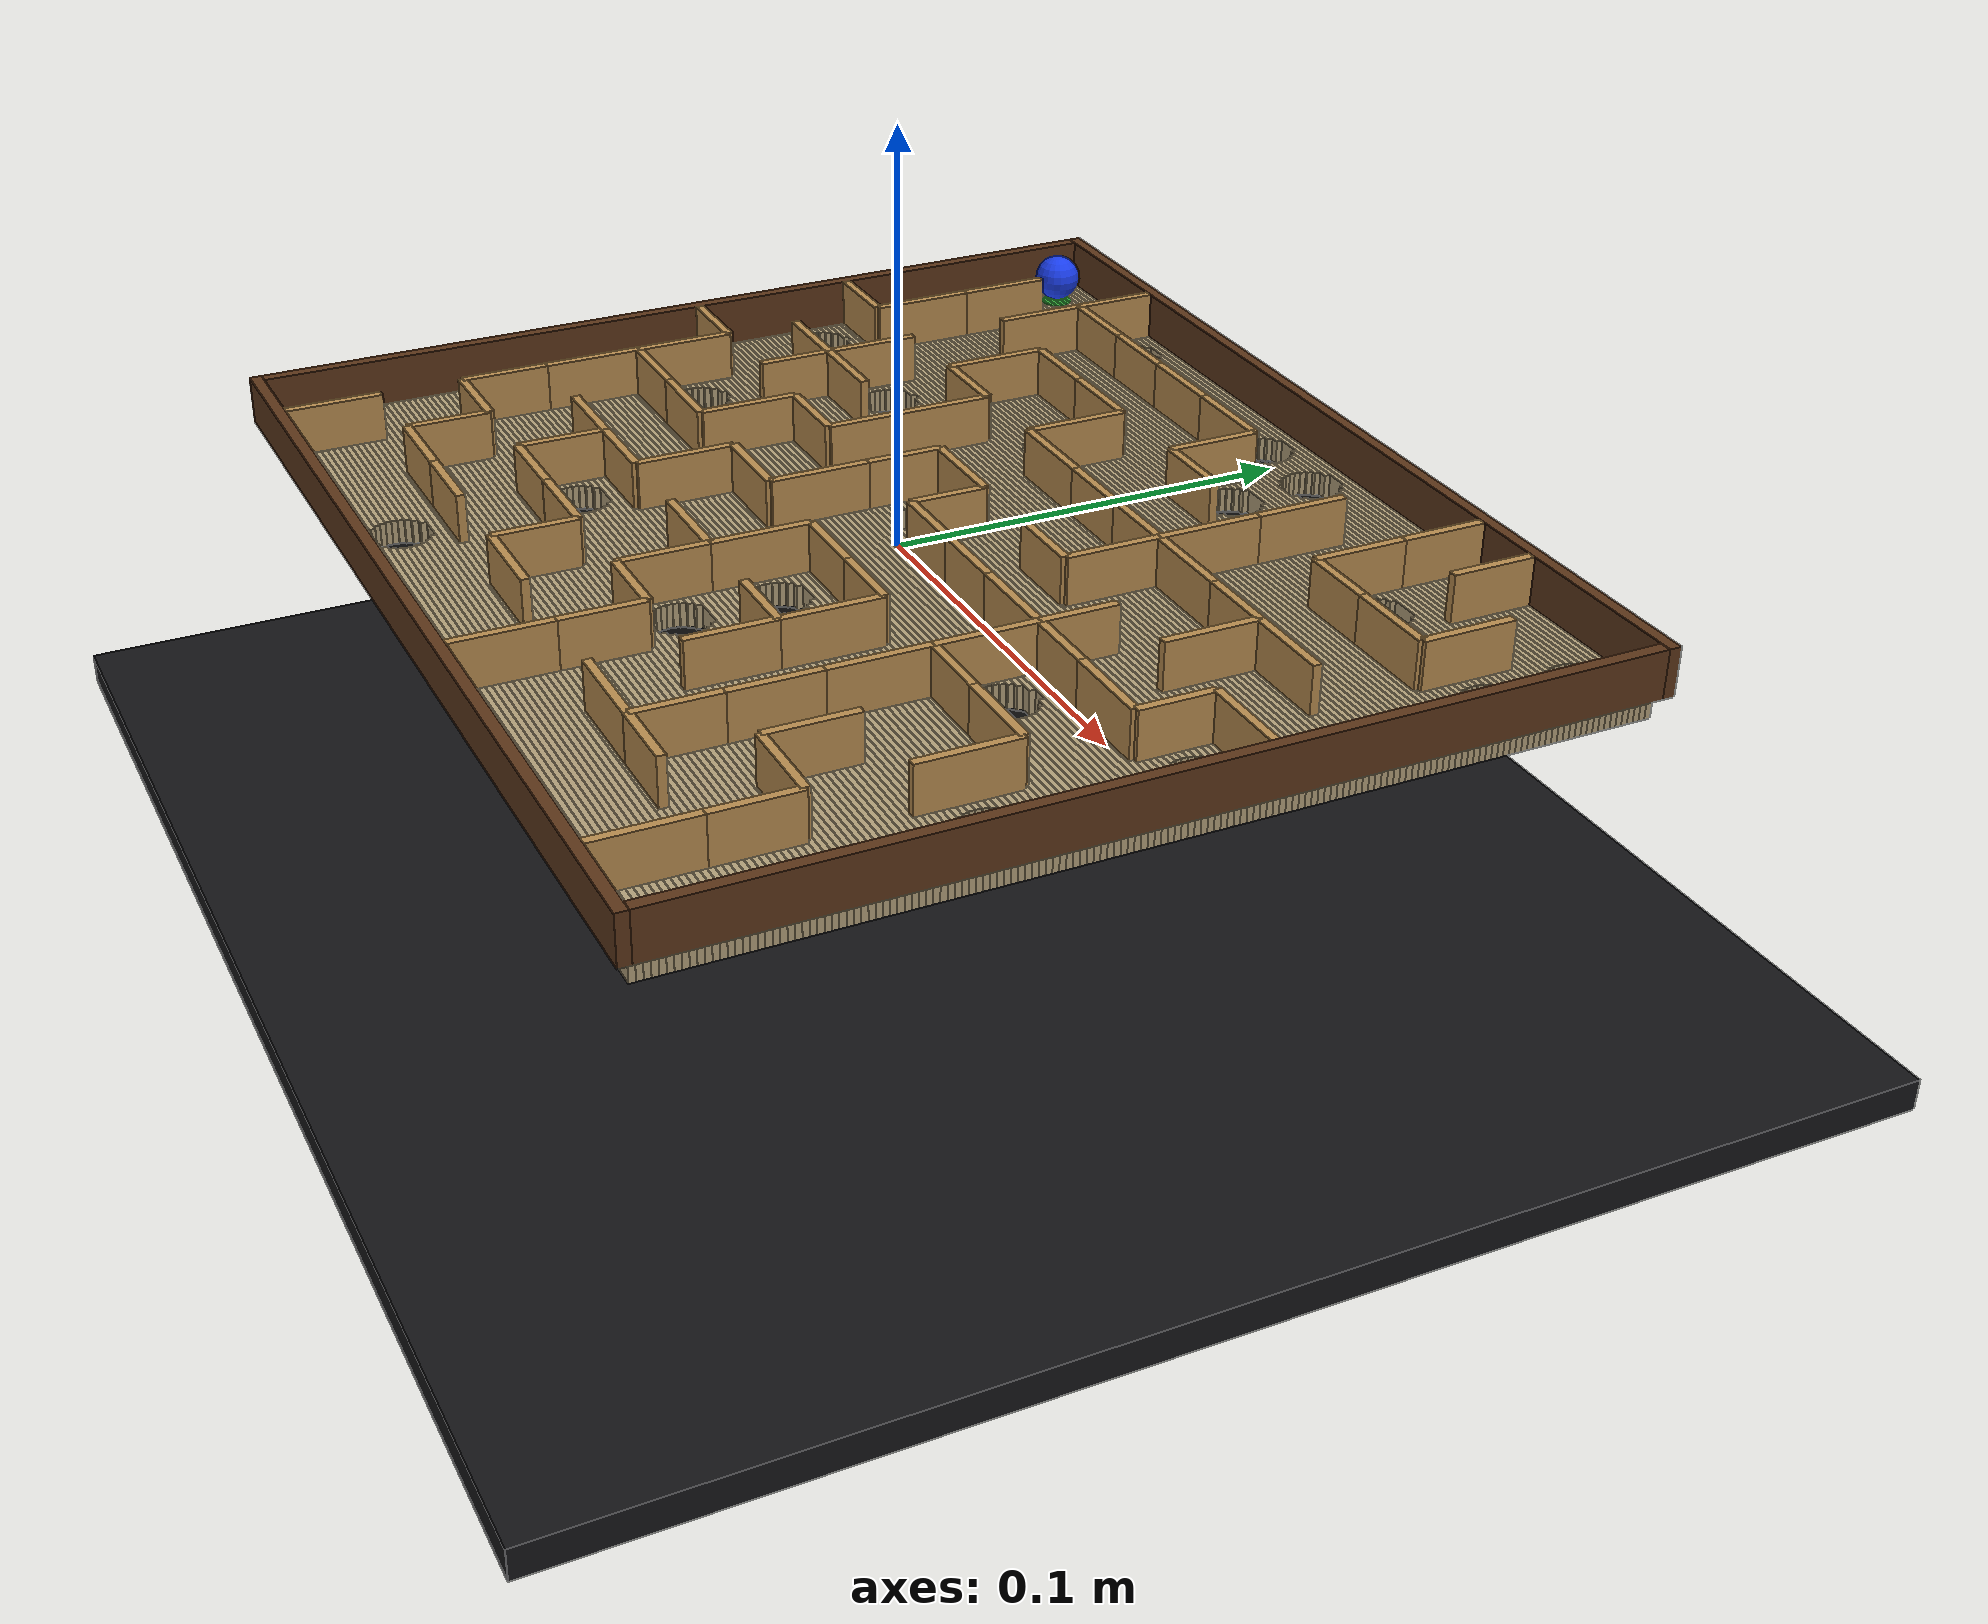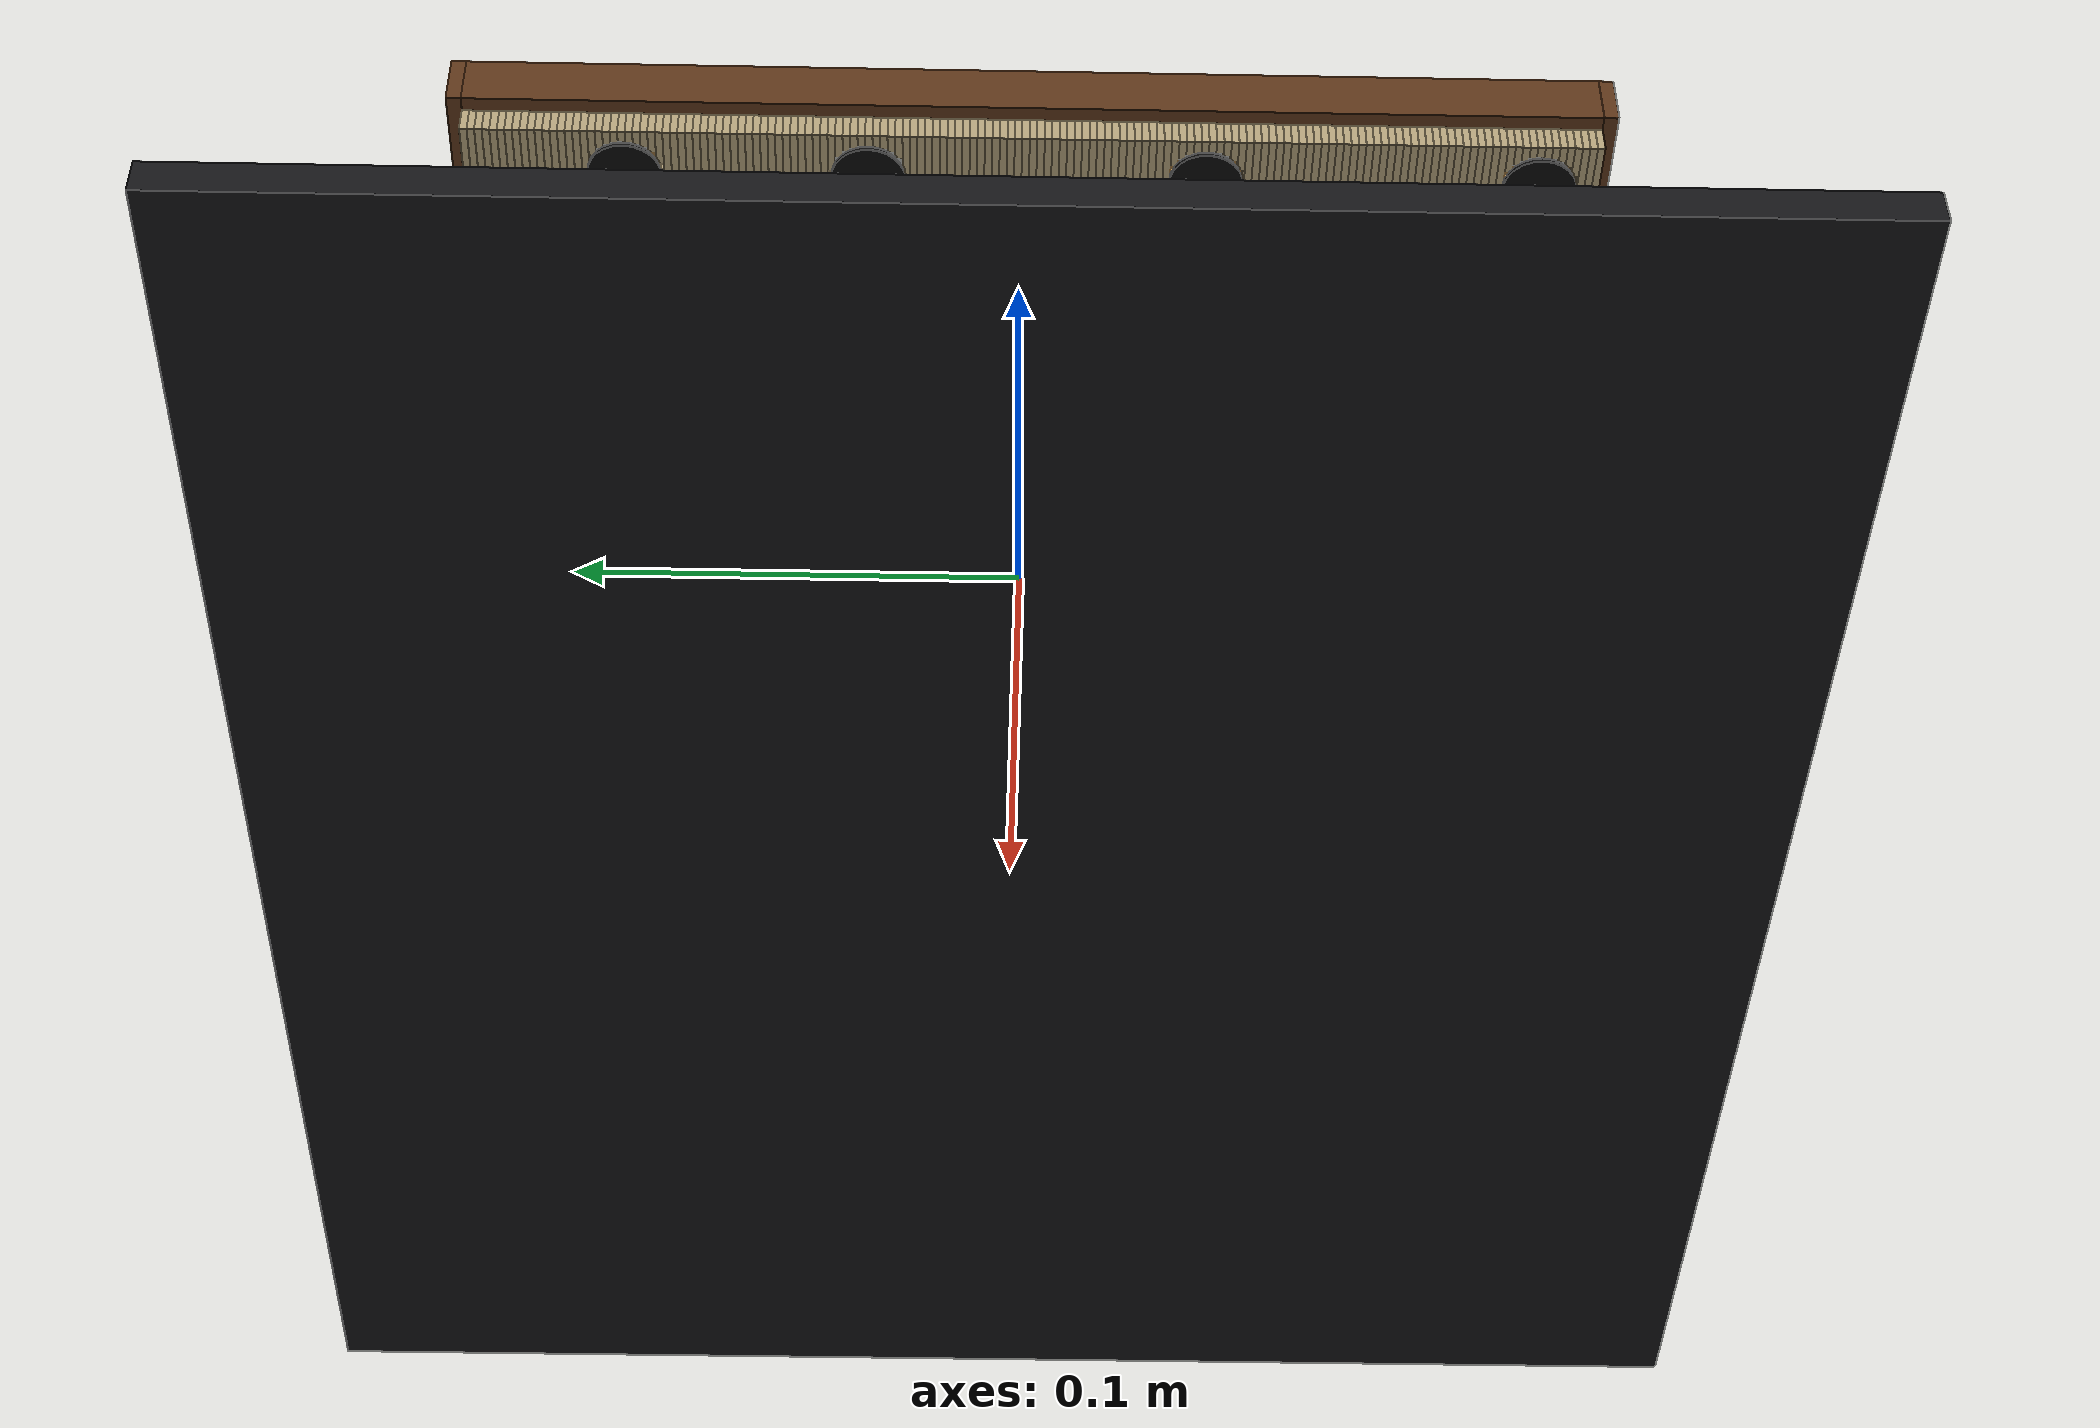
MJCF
<mujoco model="cyberrunner_custom_maze">
  <compiler angle="radian" inertiafromgeom="auto"/>
  <option timestep="0.001" gravity="0 0 -9.81" integrator="implicitfast" solver="Newton" iterations="12" tolerance="1e-9"/>
  <size nconmax="4000" njmax="12000"/>
  <visual>
    <global offwidth="900" offheight="800"/>
    <quality shadowsize="2048"/>
    <map znear="0.01" zfar="3"/>
  </visual>
  <default>
    <default class="floor">
      <geom friction="0.3 0.015 0.002" solref="0.004 1" solimp="0.95 0.99 0.001" density="650"/>
    </default>
    <default class="wall">
      <geom friction="0.35 0.02 0.003" solref="0.003 1" solimp="0.95 0.99 0.001" density="700"/>
    </default>
  </default>
  <worldbody>
    <light name="key" pos="0 -0.15 0.55" dir="0 0 -1" diffuse="0.9 0.9 0.9"/>
    <light name="fill" pos="-0.25 0.2 0.35" dir="0.4 -0.3 -1" diffuse="0.45 0.45 0.45"/>
    <camera name="top" pos="0 0 0.43" quat="1 0 0 0" mode="fixed" fovy="37"/>
    <geom name="catch_tray" type="box" pos="0 0 -0.085" size="0.18 0.16 0.004" rgba="0.08 0.08 0.09 1" friction="0.5 0.02 0.003"/>
    <body name="tilt_x_frame" pos="0 0 0">
      <inertial pos="0 0 0" mass="0.02" diaginertia="0.0001 0.0001 0.0001"/>
      <joint name="tilt_x" type="hinge" axis="1 0 0" range="-0.174532925 0.174532925" damping="0.8" armature="0.01"/>
      <body name="board" pos="0 0 0">
        <joint name="tilt_y" type="hinge" axis="0 1 0" range="-0.174532925 0.174532925" damping="0.8" armature="0.01"/>
        <geom name="floor_0" type="box" pos="0 -0.113751634 -0.003" size="0.1295 0.000748366013 0.003" rgba="0.70 0.63 0.48 1" class="floor"/><geom name="floor_1" type="box" pos="0 -0.112254902 -0.003" size="0.1295 0.000748366013 0.003" rgba="0.70 0.63 0.48 1" class="floor"/><geom name="floor_2" type="box" pos="0 -0.11075817 -0.003" size="0.1295 0.000748366013 0.003" rgba="0.70 0.63 0.48 1" class="floor"/><geom name="floor_3" type="box" pos="-0.125886508 -0.109261438 -0.003" size="0.00361349245 0.000748366013 0.003" rgba="0.70 0.63 0.48 1" class="floor"/><geom name="floor_4" type="box" pos="-0.0871621924 -0.109261438 -0.003" size="0.0292531127 0.000748366013 0.003" rgba="0.70 0.63 0.48 1" class="floor"/><geom name="floor_5" type="box" pos="0.0387243151 -0.109261438 -0.003" size="0.0907756849 0.000748366013 0.003" rgba="0.70 0.63 0.48 1" class="floor"/><geom name="floor_6" type="box" pos="-0.127020459 -0.107764706 -0.003" size="0.00247954113 0.000748366013 0.003" rgba="0.70 0.63 0.48 1" class="floor"/><geom name="floor_7" type="box" pos="-0.0871621924 -0.107764706 -0.003" size="0.0269852101 0.000748366013 0.003" rgba="0.70 0.63 0.48 1" class="floor"/><geom name="floor_8" type="box" pos="0.0398582664 -0.107764706 -0.003" size="0.0896417336 0.000748366013 0.003" rgba="0.70 0.63 0.48 1" class="floor"/><geom name="floor_9" type="box" pos="-0.127621845 -0.106267974 -0.003" size="0.00187815532 0.000748366013 0.003" rgba="0.70 0.63 0.48 1" class="floor"/><geom name="floor_10" type="box" pos="-0.0871621924 -0.106267974 -0.003" size="0.0257824384 0.000748366013 0.003" rgba="0.70 0.63 0.48 1" class="floor"/><geom name="floor_11" type="box" pos="0.0404596522 -0.106267974 -0.003" size="0.0890403478 0.000748366013 0.003" rgba="0.70 0.63 0.48 1" class="floor"/><geom name="floor_12" type="box" pos="-0.127972476 -0.104771242 -0.003" size="0.00152752399 0.000748366013 0.003" rgba="0.70 0.63 0.48 1" class="floor"/><geom name="floor_13" type="box" pos="-0.0871621924 -0.104771242 -0.003" size="0.0250811758 0.000748366013 0.003" rgba="0.70 0.63 0.48 1" class="floor"/><geom name="floor_14" type="box" pos="0.0408102836 -0.104771242 -0.003" size="0.0886897164 0.000748366013 0.003" rgba="0.70 0.63 0.48 1" class="floor"/><geom name="floor_15" type="box" pos="-0.128143911 -0.10327451 -0.003" size="0.00135608897 0.000748366013 0.003" rgba="0.70 0.63 0.48 1" class="floor"/><geom name="floor_16" type="box" pos="-0.0871621924 -0.10327451 -0.003" size="0.0247383057 0.000748366013 0.003" rgba="0.70 0.63 0.48 1" class="floor"/><geom name="floor_17" type="box" pos="0.0409817186 -0.10327451 -0.003" size="0.0885182814 0.000748366013 0.003" rgba="0.70 0.63 0.48 1" class="floor"/><geom name="floor_18" type="box" pos="-0.128160882 -0.101777778 -0.003" size="0.00133911842 0.000748366013 0.003" rgba="0.70 0.63 0.48 1" class="floor"/><geom name="floor_19" type="box" pos="-0.0871621924 -0.101777778 -0.003" size="0.0247043646 0.000748366013 0.003" rgba="0.70 0.63 0.48 1" class="floor"/><geom name="floor_20" type="box" pos="0.0409986891 -0.101777778 -0.003" size="0.0885013109 0.000748366013 0.003" rgba="0.70 0.63 0.48 1" class="floor"/><geom name="floor_21" type="box" pos="-0.128025571 -0.100281046 -0.003" size="0.00147442934 0.000748366013 0.003" rgba="0.70 0.63 0.48 1" class="floor"/><geom name="floor_22" type="box" pos="-0.0871621924 -0.100281046 -0.003" size="0.0249749865 0.000748366013 0.003" rgba="0.70 0.63 0.48 1" class="floor"/><geom name="floor_23" type="box" pos="0.0408633782 -0.100281046 -0.003" size="0.0886366218 0.000748366013 0.003" rgba="0.70 0.63 0.48 1" class="floor"/><geom name="floor_24" type="box" pos="-0.127719283 -0.0987843137 -0.003" size="0.00178071677 0.000748366013 0.003" rgba="0.70 0.63 0.48 1" class="floor"/><geom name="floor_25" type="box" pos="-0.0871621924 -0.0987843137 -0.003" size="0.0255875613 0.000748366013 0.003" rgba="0.70 0.63 0.48 1" class="floor"/><geom name="floor_26" type="box" pos="0.0405570908 -0.0987843137 -0.003" size="0.0889429092 0.000748366013 0.003" rgba="0.70 0.63 0.48 1" class="floor"/><geom name="floor_27" type="box" pos="-0.127185746 -0.0972875817 -0.003" size="0.00231425396 0.000748366013 0.003" rgba="0.70 0.63 0.48 1" class="floor"/><geom name="floor_28" type="box" pos="-0.0871621924 -0.0972875817 -0.003" size="0.0266546357 0.000748366013 0.003" rgba="0.70 0.63 0.48 1" class="floor"/><geom name="floor_29" type="box" pos="0.0400235536 -0.0972875817 -0.003" size="0.0894764464 0.000748366013 0.003" rgba="0.70 0.63 0.48 1" class="floor"/><geom name="floor_30" type="box" pos="-0.126234274 -0.0957908497 -0.003" size="0.00326572591 0.000748366013 0.003" rgba="0.70 0.63 0.48 1" class="floor"/><geom name="floor_31" type="box" pos="-0.0871621924 -0.0957908497 -0.003" size="0.0285575796 0.000748366013 0.003" rgba="0.70 0.63 0.48 1" class="floor"/><geom name="floor_32" type="box" pos="0.0390720816 -0.0957908497 -0.003" size="0.0904279184 0.000748366013 0.003" rgba="0.70 0.63 0.48 1" class="floor"/><geom name="floor_33" type="box" pos="0 -0.0942941176 -0.003" size="0.1295 0.000748366013 0.003" rgba="0.70 0.63 0.48 1" class="floor"/><geom name="floor_34" type="box" pos="0 -0.0927973856 -0.003" size="0.1295 0.000748366013 0.003" rgba="0.70 0.63 0.48 1" class="floor"/><geom name="floor_35" type="box" pos="0 -0.0913006536 -0.003" size="0.1295 0.000748366013 0.003" rgba="0.70 0.63 0.48 1" class="floor"/><geom name="floor_36" type="box" pos="0 -0.0898039216 -0.003" size="0.1295 0.000748366013 0.003" rgba="0.70 0.63 0.48 1" class="floor"/><geom name="floor_37" type="box" pos="0 -0.0883071895 -0.003" size="0.1295 0.000748366013 0.003" rgba="0.70 0.63 0.48 1" class="floor"/><geom name="floor_38" type="box" pos="-0.115268128 -0.0868104575 -0.003" size="0.0142318722 0.000748366013 0.003" rgba="0.70 0.63 0.48 1" class="floor"/><geom name="floor_39" type="box" pos="0.0169947867 -0.0868104575 -0.003" size="0.112505213 0.000748366013 0.003" rgba="0.70 0.63 0.48 1" class="floor"/><geom name="floor_40" type="box" pos="-0.116449166 -0.0853137255 -0.003" size="0.0130508338 0.000748366013 0.003" rgba="0.70 0.63 0.48 1" class="floor"/><geom name="floor_41" type="box" pos="0.0181758251 -0.0853137255 -0.003" size="0.111324175 0.000748366013 0.003" rgba="0.70 0.63 0.48 1" class="floor"/><geom name="floor_42" type="box" pos="-0.117065387 -0.0838169935 -0.003" size="0.0124346127 0.000748366013 0.003" rgba="0.70 0.63 0.48 1" class="floor"/><geom name="floor_43" type="box" pos="0.0187920462 -0.0838169935 -0.003" size="0.110707954 0.000748366013 0.003" rgba="0.70 0.63 0.48 1" class="floor"/><geom name="floor_44" type="box" pos="-0.117425313 -0.0823202614 -0.003" size="0.0120746866 0.000748366013 0.003" rgba="0.70 0.63 0.48 1" class="floor"/><geom name="floor_45" type="box" pos="0.0191519723 -0.0823202614 -0.003" size="0.110348028 0.000748366013 0.003" rgba="0.70 0.63 0.48 1" class="floor"/><geom name="floor_46" type="box" pos="-0.117604149 -0.0808235294 -0.003" size="0.0118958515 0.000748366013 0.003" rgba="0.70 0.63 0.48 1" class="floor"/><geom name="floor_47" type="box" pos="0.0193308075 -0.0808235294 -0.003" size="0.110169193 0.000748366013 0.003" rgba="0.70 0.63 0.48 1" class="floor"/><geom name="floor_48" type="box" pos="-0.117627952 -0.0793267974 -0.003" size="0.0118720478 0.000748366013 0.003" rgba="0.70 0.63 0.48 1" class="floor"/><geom name="floor_49" type="box" pos="0.0193546112 -0.0793267974 -0.003" size="0.110145389 0.000748366013 0.003" rgba="0.70 0.63 0.48 1" class="floor"/><geom name="floor_50" type="box" pos="-0.11749979 -0.0778300654 -0.003" size="0.0120002101 0.000748366013 0.003" rgba="0.70 0.63 0.48 1" class="floor"/><geom name="floor_51" type="box" pos="0.0192264489 -0.0778300654 -0.003" size="0.110273551 0.000748366013 0.003" rgba="0.70 0.63 0.48 1" class="floor"/><geom name="floor_52" type="box" pos="-0.117202085 -0.0763333333 -0.003" size="0.0122979153 0.000748366013 0.003" rgba="0.70 0.63 0.48 1" class="floor"/><geom name="floor_53" type="box" pos="0.0189287436 -0.0763333333 -0.003" size="0.110571256 0.000748366013 0.003" rgba="0.70 0.63 0.48 1" class="floor"/><geom name="floor_54" type="box" pos="-0.116681166 -0.0748366013 -0.003" size="0.0128188336 0.000748366013 0.003" rgba="0.70 0.63 0.48 1" class="floor"/><geom name="floor_55" type="box" pos="0.0184078253 -0.0748366013 -0.003" size="0.111092175 0.000748366013 0.003" rgba="0.70 0.63 0.48 1" class="floor"/><geom name="floor_56" type="box" pos="-0.115759193 -0.0733398693 -0.003" size="0.0137408072 0.000748366013 0.003" rgba="0.70 0.63 0.48 1" class="floor"/><geom name="floor_57" type="box" pos="0.0174858518 -0.0733398693 -0.003" size="0.112014148 0.000748366013 0.003" rgba="0.70 0.63 0.48 1" class="floor"/><geom name="floor_58" type="box" pos="0 -0.0718431373 -0.003" size="0.1295 0.000748366013 0.003" rgba="0.70 0.63 0.48 1" class="floor"/><geom name="floor_59" type="box" pos="0 -0.0703464052 -0.003" size="0.1295 0.000748366013 0.003" rgba="0.70 0.63 0.48 1" class="floor"/><geom name="floor_60" type="box" pos="0 -0.0688496732 -0.003" size="0.1295 0.000748366013 0.003" rgba="0.70 0.63 0.48 1" class="floor"/><geom name="floor_61" type="box" pos="0 -0.0673529412 -0.003" size="0.1295 0.000748366013 0.003" rgba="0.70 0.63 0.48 1" class="floor"/><geom name="floor_62" type="box" pos="-0.0927291173 -0.0658562092 -0.003" size="0.0367708827 0.000748366013 0.003" rgba="0.70 0.63 0.48 1" class="floor"/><geom name="floor_63" type="box" pos="-0.0214784928 -0.0658562092 -0.003" size="0.0325237221 0.000748366013 0.003" rgba="0.70 0.63 0.48 1" class="floor"/><geom name="floor_64" type="box" pos="0.0219440632 -0.0658562092 -0.003" size="0.0089428141 0.000748366013 0.003" rgba="0.70 0.63 0.48 1" class="floor"/><geom name="floor_65" type="box" pos="0.0811714485 -0.0658562092 -0.003" size="0.0483285515 0.000748366013 0.003" rgba="0.70 0.63 0.48 1" class="floor"/><geom name="floor_66" type="box" pos="-0.0945300673 -0.0643594771 -0.003" size="0.0349699327 0.000748366013 0.003" rgba="0.70 0.63 0.48 1" class="floor"/><geom name="floor_67" type="box" pos="-0.0214784928 -0.0643594771 -0.003" size="0.0289218221 0.000748366013 0.003" rgba="0.70 0.63 0.48 1" class="floor"/><geom name="floor_68" type="box" pos="0.0219440632 -0.0643594771 -0.003" size="0.0053409141 0.000748366013 0.003" rgba="0.70 0.63 0.48 1" class="floor"/><geom name="floor_69" type="box" pos="0.0829723985 -0.0643594771 -0.003" size="0.0465276015 0.000748366013 0.003" rgba="0.70 0.63 0.48 1" class="floor"/><geom name="floor_70" type="box" pos="-0.0952614628 -0.0628627451 -0.003" size="0.0342385372 0.000748366013 0.003" rgba="0.70 0.63 0.48 1" class="floor"/><geom name="floor_71" type="box" pos="-0.0214784928 -0.0628627451 -0.003" size="0.0274590312 0.000748366013 0.003" rgba="0.70 0.63 0.48 1" class="floor"/><geom name="floor_72" type="box" pos="0.0219440632 -0.0628627451 -0.003" size="0.00387812324 0.000748366013 0.003" rgba="0.70 0.63 0.48 1" class="floor"/><geom name="floor_73" type="box" pos="0.083703794 -0.0628627451 -0.003" size="0.045796206 0.000748366013 0.003" rgba="0.70 0.63 0.48 1" class="floor"/><geom name="floor_74" type="box" pos="-0.0956887526 -0.0613660131 -0.003" size="0.0338112474 0.000748366013 0.003" rgba="0.70 0.63 0.48 1" class="floor"/><geom name="floor_75" type="box" pos="-0.0214784928 -0.0613660131 -0.003" size="0.0266044516 0.000748366013 0.003" rgba="0.70 0.63 0.48 1" class="floor"/><geom name="floor_76" type="box" pos="0.0219440632 -0.0613660131 -0.003" size="0.00302354361 0.000748366013 0.003" rgba="0.70 0.63 0.48 1" class="floor"/><geom name="floor_77" type="box" pos="0.0841310838 -0.0613660131 -0.003" size="0.0453689162 0.000748366013 0.003" rgba="0.70 0.63 0.48 1" class="floor"/><geom name="floor_78" type="box" pos="-0.095919457 -0.059869281 -0.003" size="0.033580543 0.000748366013 0.003" rgba="0.70 0.63 0.48 1" class="floor"/><geom name="floor_79" type="box" pos="-0.0214784928 -0.059869281 -0.003" size="0.0261430427 0.000748366013 0.003" rgba="0.70 0.63 0.48 1" class="floor"/><geom name="floor_80" type="box" pos="0.0219440632 -0.059869281 -0.003" size="0.00256213474 0.000748366013 0.003" rgba="0.70 0.63 0.48 1" class="floor"/><geom name="floor_81" type="box" pos="0.0843617882 -0.059869281 -0.003" size="0.0451382118 0.000748366013 0.003" rgba="0.70 0.63 0.48 1" class="floor"/><geom name="floor_82" type="box" pos="-0.0959900365 -0.058372549 -0.003" size="0.0335099635 0.000748366013 0.003" rgba="0.70 0.63 0.48 1" class="floor"/><geom name="floor_83" type="box" pos="-0.0214784928 -0.058372549 -0.003" size="0.0260018837 0.000748366013 0.003" rgba="0.70 0.63 0.48 1" class="floor"/><geom name="floor_84" type="box" pos="0.0219440632 -0.058372549 -0.003" size="0.00242097568 0.000748366013 0.003" rgba="0.70 0.63 0.48 1" class="floor"/><geom name="floor_85" type="box" pos="0.0844323677 -0.058372549 -0.003" size="0.0450676323 0.000748366013 0.003" rgba="0.70 0.63 0.48 1" class="floor"/><geom name="floor_86" type="box" pos="-0.0959097421 -0.056875817 -0.003" size="0.0335902579 0.000748366013 0.003" rgba="0.70 0.63 0.48 1" class="floor"/><geom name="floor_87" type="box" pos="-0.0214784928 -0.056875817 -0.003" size="0.0261624726 0.000748366013 0.003" rgba="0.70 0.63 0.48 1" class="floor"/><geom name="floor_88" type="box" pos="0.0219440632 -0.056875817 -0.003" size="0.0025815646 0.000748366013 0.003" rgba="0.70 0.63 0.48 1" class="floor"/><geom name="floor_89" type="box" pos="0.0843520733 -0.056875817 -0.003" size="0.0451479267 0.000748366013 0.003" rgba="0.70 0.63 0.48 1" class="floor"/><geom name="floor_90" type="box" pos="-0.0956679878 -0.055379085 -0.003" size="0.0338320122 0.000748366013 0.003" rgba="0.70 0.63 0.48 1" class="floor"/><geom name="floor_91" type="box" pos="-0.0214784928 -0.055379085 -0.003" size="0.0266459812 0.000748366013 0.003" rgba="0.70 0.63 0.48 1" class="floor"/><geom name="floor_92" type="box" pos="0.0219440632 -0.055379085 -0.003" size="0.00306507322 0.000748366013 0.003" rgba="0.70 0.63 0.48 1" class="floor"/><geom name="floor_93" type="box" pos="0.084110319 -0.055379085 -0.003" size="0.045389681 0.000748366013 0.003" rgba="0.70 0.63 0.48 1" class="floor"/><geom name="floor_94" type="box" pos="-0.0952258072 -0.0538823529 -0.003" size="0.0342741928 0.000748366013 0.003" rgba="0.70 0.63 0.48 1" class="floor"/><geom name="floor_95" type="box" pos="-0.0214784928 -0.0538823529 -0.003" size="0.0275303422 0.000748366013 0.003" rgba="0.70 0.63 0.48 1" class="floor"/><geom name="floor_96" type="box" pos="0.0219440632 -0.0538823529 -0.003" size="0.00394943427 0.000748366013 0.003" rgba="0.70 0.63 0.48 1" class="floor"/><geom name="floor_97" type="box" pos="0.0836681384 -0.0538823529 -0.003" size="0.0458318616 0.000748366013 0.003" rgba="0.70 0.63 0.48 1" class="floor"/><geom name="floor_98" type="box" pos="-0.0944668397 -0.0523856209 -0.003" size="0.0350331603 0.000748366013 0.003" rgba="0.70 0.63 0.48 1" class="floor"/><geom name="floor_99" type="box" pos="-0.0214784928 -0.0523856209 -0.003" size="0.0290482773 0.000748366013 0.003" rgba="0.70 0.63 0.48 1" class="floor"/><geom name="floor_100" type="box" pos="0.0219440632 -0.0523856209 -0.003" size="0.00546736933 0.000748366013 0.003" rgba="0.70 0.63 0.48 1" class="floor"/><geom name="floor_101" type="box" pos="0.0829091709 -0.0523856209 -0.003" size="0.0465908291 0.000748366013 0.003" rgba="0.70 0.63 0.48 1" class="floor"/><geom name="floor_102" type="box" pos="0 -0.0508888889 -0.003" size="0.1295 0.000748366013 0.003" rgba="0.70 0.63 0.48 1" class="floor"/><geom name="floor_103" type="box" pos="0 -0.0493921569 -0.003" size="0.1295 0.000748366013 0.003" rgba="0.70 0.63 0.48 1" class="floor"/><geom name="floor_104" type="box" pos="0 -0.0478954248 -0.003" size="0.1295 0.000748366013 0.003" rgba="0.70 0.63 0.48 1" class="floor"/><geom name="floor_105" type="box" pos="0 -0.0463986928 -0.003" size="0.1295 0.000748366013 0.003" rgba="0.70 0.63 0.48 1" class="floor"/><geom name="floor_106" type="box" pos="0 -0.0449019608 -0.003" size="0.1295 0.000748366013 0.003" rgba="0.70 0.63 0.48 1" class="floor"/><geom name="floor_107" type="box" pos="0 -0.0434052288 -0.003" size="0.1295 0.000748366013 0.003" rgba="0.70 0.63 0.48 1" class="floor"/><geom name="floor_108" type="box" pos="-0.125884786 -0.0419084967 -0.003" size="0.00361521381 0.000748366013 0.003" rgba="0.70 0.63 0.48 1" class="floor"/><geom name="floor_109" type="box" pos="-0.0536604605 -0.0419084967 -0.003" size="0.0627582874 0.000748366013 0.003" rgba="0.70 0.63 0.48 1" class="floor"/><geom name="floor_110" type="box" pos="0.0219440632 -0.0419084967 -0.003" size="0.00699541173 0.000748366013 0.003" rgba="0.70 0.63 0.48 1" class="floor"/><geom name="floor_111" type="box" pos="0.0751280418 -0.0419084967 -0.003" size="0.0403377424 0.000748366013 0.003" rgba="0.70 0.63 0.48 1" class="floor"/><geom name="floor_112" type="box" pos="0.125408304 -0.0419084967 -0.003" size="0.00409169568 0.000748366013 0.003" rgba="0.70 0.63 0.48 1" class="floor"/><geom name="floor_113" type="box" pos="-0.127019699 -0.0404117647 -0.003" size="0.00248030066 0.000748366013 0.003" rgba="0.70 0.63 0.48 1" class="floor"/><geom name="floor_114" type="box" pos="-0.0536604605 -0.0404117647 -0.003" size="0.0604884611 0.000748366013 0.003" rgba="0.70 0.63 0.48 1" class="floor"/><geom name="floor_115" type="box" pos="0.0219440632 -0.0404117647 -0.003" size="0.00472558543 0.000748366013 0.003" rgba="0.70 0.63 0.48 1" class="floor"/><geom name="floor_116" type="box" pos="0.0751280418 -0.0404117647 -0.003" size="0.0380679161 0.000748366013 0.003" rgba="0.70 0.63 0.48 1" class="floor"/><geom name="floor_117" type="box" pos="0.126543217 -0.0404117647 -0.003" size="0.00295678253 0.000748366013 0.003" rgba="0.70 0.63 0.48 1" class="floor"/><geom name="floor_118" type="box" pos="-0.127621399 -0.0389150327 -0.003" size="0.00187860138 0.000748366013 0.003" rgba="0.70 0.63 0.48 1" class="floor"/><geom name="floor_119" type="box" pos="-0.0536604605 -0.0389150327 -0.003" size="0.0592850625 0.000748366013 0.003" rgba="0.70 0.63 0.48 1" class="floor"/><geom name="floor_120" type="box" pos="0.0219440632 -0.0389150327 -0.003" size="0.00352218687 0.000748366013 0.003" rgba="0.70 0.63 0.48 1" class="floor"/><geom name="floor_121" type="box" pos="0.0751280418 -0.0389150327 -0.003" size="0.0368645175 0.000748366013 0.003" rgba="0.70 0.63 0.48 1" class="floor"/><geom name="floor_122" type="box" pos="0.127144917 -0.0389150327 -0.003" size="0.00235508325 0.000748366013 0.003" rgba="0.70 0.63 0.48 1" class="floor"/><geom name="floor_123" type="box" pos="-0.127972228 -0.0374183007 -0.003" size="0.00152777217 0.000748366013 0.003" rgba="0.70 0.63 0.48 1" class="floor"/><geom name="floor_124" type="box" pos="-0.0536604605 -0.0374183007 -0.003" size="0.0585834041 0.000748366013 0.003" rgba="0.70 0.63 0.48 1" class="floor"/><geom name="floor_125" type="box" pos="0.0219440632 -0.0374183007 -0.003" size="0.00282052845 0.000748366013 0.003" rgba="0.70 0.63 0.48 1" class="floor"/><geom name="floor_126" type="box" pos="0.0751280418 -0.0374183007 -0.003" size="0.0361628591 0.000748366013 0.003" rgba="0.70 0.63 0.48 1" class="floor"/><geom name="floor_127" type="box" pos="0.127495746 -0.0374183007 -0.003" size="0.00200425404 0.000748366013 0.003" rgba="0.70 0.63 0.48 1" class="floor"/><geom name="floor_128" type="box" pos="-0.128143821 -0.0359215686 -0.003" size="0.00135617898 0.000748366013 0.003" rgba="0.70 0.63 0.48 1" class="floor"/><geom name="floor_129" type="box" pos="-0.0536604605 -0.0359215686 -0.003" size="0.0582402177 0.000748366013 0.003" rgba="0.70 0.63 0.48 1" class="floor"/><geom name="floor_130" type="box" pos="0.0219440632 -0.0359215686 -0.003" size="0.00247734208 0.000748366013 0.003" rgba="0.70 0.63 0.48 1" class="floor"/><geom name="floor_131" type="box" pos="0.0751280418 -0.0359215686 -0.003" size="0.0358196727 0.000748366013 0.003" rgba="0.70 0.63 0.48 1" class="floor"/><geom name="floor_132" type="box" pos="0.127667339 -0.0359215686 -0.003" size="0.00183266086 0.000748366013 0.003" rgba="0.70 0.63 0.48 1" class="floor"/><geom name="floor_133" type="box" pos="-0.128160938 -0.0344248366 -0.003" size="0.00133906197 0.000748366013 0.003" rgba="0.70 0.63 0.48 1" class="floor"/><geom name="floor_134" type="box" pos="-0.0536604605 -0.0344248366 -0.003" size="0.0582059837 0.000748366013 0.003" rgba="0.70 0.63 0.48 1" class="floor"/><geom name="floor_135" type="box" pos="0.0219440632 -0.0344248366 -0.003" size="0.00244310805 0.000748366013 0.003" rgba="0.70 0.63 0.48 1" class="floor"/><geom name="floor_136" type="box" pos="0.0751280418 -0.0344248366 -0.003" size="0.0357854387 0.000748366013 0.003" rgba="0.70 0.63 0.48 1" class="floor"/><geom name="floor_137" type="box" pos="0.127684456 -0.0344248366 -0.003" size="0.00181554384 0.000748366013 0.003" rgba="0.70 0.63 0.48 1" class="floor"/><geom name="floor_138" type="box" pos="-0.128025781 -0.0329281046 -0.003" size="0.00147421924 0.000748366013 0.003" rgba="0.70 0.63 0.48 1" class="floor"/><geom name="floor_139" type="box" pos="-0.0536604605 -0.0329281046 -0.003" size="0.0584762982 0.000748366013 0.003" rgba="0.70 0.63 0.48 1" class="floor"/><geom name="floor_140" type="box" pos="0.0219440632 -0.0329281046 -0.003" size="0.00271342259 0.000748366013 0.003" rgba="0.70 0.63 0.48 1" class="floor"/><geom name="floor_141" type="box" pos="0.0751280418 -0.0329281046 -0.003" size="0.0360557532 0.000748366013 0.003" rgba="0.70 0.63 0.48 1" class="floor"/><geom name="floor_142" type="box" pos="0.127549299 -0.0329281046 -0.003" size="0.00195070111 0.000748366013 0.003" rgba="0.70 0.63 0.48 1" class="floor"/><geom name="floor_143" type="box" pos="-0.127719678 -0.0314313725 -0.003" size="0.00178032155 0.000748366013 0.003" rgba="0.70 0.63 0.48 1" class="floor"/><geom name="floor_144" type="box" pos="-0.0536604605 -0.0314313725 -0.003" size="0.0590885029 0.000748366013 0.003" rgba="0.70 0.63 0.48 1" class="floor"/><geom name="floor_145" type="box" pos="0.0219440632 -0.0314313725 -0.003" size="0.0033256272 0.000748366013 0.003" rgba="0.70 0.63 0.48 1" class="floor"/><geom name="floor_146" type="box" pos="0.0751280418 -0.0314313725 -0.003" size="0.0366679578 0.000748366013 0.003" rgba="0.70 0.63 0.48 1" class="floor"/><geom name="floor_147" type="box" pos="0.127243197 -0.0314313725 -0.003" size="0.00225680342 0.000748366013 0.003" rgba="0.70 0.63 0.48 1" class="floor"/><geom name="floor_148" type="box" pos="-0.127186415 -0.0299346405 -0.003" size="0.0023135849 0.000748366013 0.003" rgba="0.70 0.63 0.48 1" class="floor"/><geom name="floor_149" type="box" pos="-0.0536604605 -0.0299346405 -0.003" size="0.0601550296 0.000748366013 0.003" rgba="0.70 0.63 0.48 1" class="floor"/><geom name="floor_150" type="box" pos="0.0219440632 -0.0299346405 -0.003" size="0.00439215391 0.000748366013 0.003" rgba="0.70 0.63 0.48 1" class="floor"/><geom name="floor_151" type="box" pos="0.0751280418 -0.0299346405 -0.003" size="0.0377344845 0.000748366013 0.003" rgba="0.70 0.63 0.48 1" class="floor"/><geom name="floor_152" type="box" pos="0.126709933 -0.0299346405 -0.003" size="0.00279006677 0.000748366013 0.003" rgba="0.70 0.63 0.48 1" class="floor"/><geom name="floor_153" type="box" pos="-0.126235595 -0.0284379085 -0.003" size="0.0032644046 0.000748366013 0.003" rgba="0.70 0.63 0.48 1" class="floor"/><geom name="floor_154" type="box" pos="-0.0536604605 -0.0284379085 -0.003" size="0.062056669 0.000748366013 0.003" rgba="0.70 0.63 0.48 1" class="floor"/><geom name="floor_155" type="box" pos="0.0219440632 -0.0284379085 -0.003" size="0.00629379331 0.000748366013 0.003" rgba="0.70 0.63 0.48 1" class="floor"/><geom name="floor_156" type="box" pos="0.0751280418 -0.0284379085 -0.003" size="0.0396361239 0.000748366013 0.003" rgba="0.70 0.63 0.48 1" class="floor"/><geom name="floor_157" type="box" pos="0.125759114 -0.0284379085 -0.003" size="0.00374088647 0.000748366013 0.003" rgba="0.70 0.63 0.48 1" class="floor"/><geom name="floor_158" type="box" pos="0 -0.0269411765 -0.003" size="0.1295 0.000748366013 0.003" rgba="0.70 0.63 0.48 1" class="floor"/><geom name="floor_159" type="box" pos="0 -0.0254444444 -0.003" size="0.1295 0.000748366013 0.003" rgba="0.70 0.63 0.48 1" class="floor"/><geom name="floor_160" type="box" pos="0 -0.0239477124 -0.003" size="0.1295 0.000748366013 0.003" rgba="0.70 0.63 0.48 1" class="floor"/><geom name="floor_161" type="box" pos="0 -0.0224509804 -0.003" size="0.1295 0.000748366013 0.003" rgba="0.70 0.63 0.48 1" class="floor"/><geom name="floor_162" type="box" pos="0 -0.0209542484 -0.003" size="0.1295 0.000748366013 0.003" rgba="0.70 0.63 0.48 1" class="floor"/><geom name="floor_163" type="box" pos="0 -0.0194575163 -0.003" size="0.1295 0.000748366013 0.003" rgba="0.70 0.63 0.48 1" class="floor"/><geom name="floor_164" type="box" pos="0 -0.0179607843 -0.003" size="0.1295 0.000748366013 0.003" rgba="0.70 0.63 0.48 1" class="floor"/><geom name="floor_165" type="box" pos="-0.115945529 -0.0164640523 -0.003" size="0.0135544708 0.000748366013 0.003" rgba="0.70 0.63 0.48 1" class="floor"/><geom name="floor_166" type="box" pos="-0.0873416327 -0.0164640523 -0.003" size="0.00681399104 0.000748366013 0.003" rgba="0.70 0.63 0.48 1" class="floor"/><geom name="floor_167" type="box" pos="-0.000627344937 -0.0164640523 -0.003" size="0.0716648622 0.000748366013 0.003" rgba="0.70 0.63 0.48 1" class="floor"/><geom name="floor_168" type="box" pos="0.104386476 -0.0164640523 -0.003" size="0.0251135241 0.000748366013 0.003" rgba="0.70 0.63 0.48 1" class="floor"/><geom name="floor_169" type="box" pos="-0.116779765 -0.0149673203 -0.003" size="0.0127202346 0.000748366013 0.003" rgba="0.70 0.63 0.48 1" class="floor"/><geom name="floor_170" type="box" pos="-0.0873416327 -0.0149673203 -0.003" size="0.00514551848 0.000748366013 0.003" rgba="0.70 0.63 0.48 1" class="floor"/><geom name="floor_171" type="box" pos="-0.000627344937 -0.0149673203 -0.003" size="0.0699963897 0.000748366013 0.003" rgba="0.70 0.63 0.48 1" class="floor"/><geom name="floor_172" type="box" pos="0.105220712 -0.0149673203 -0.003" size="0.0242792878 0.000748366013 0.003" rgba="0.70 0.63 0.48 1" class="floor"/><geom name="floor_173" type="box" pos="-0.117260243 -0.0134705882 -0.003" size="0.0122397566 0.000748366013 0.003" rgba="0.70 0.63 0.48 1" class="floor"/><geom name="floor_174" type="box" pos="-0.0873416327 -0.0134705882 -0.003" size="0.00418456251 0.000748366013 0.003" rgba="0.70 0.63 0.48 1" class="floor"/><geom name="floor_175" type="box" pos="-0.000627344937 -0.0134705882 -0.003" size="0.0690354337 0.000748366013 0.003" rgba="0.70 0.63 0.48 1" class="floor"/><geom name="floor_176" type="box" pos="0.10570119 -0.0134705882 -0.003" size="0.0237988098 0.000748366013 0.003" rgba="0.70 0.63 0.48 1" class="floor"/><geom name="floor_177" type="box" pos="-0.117529731 -0.0119738562 -0.003" size="0.0119702694 0.000748366013 0.003" rgba="0.70 0.63 0.48 1" class="floor"/><geom name="floor_178" type="box" pos="-0.0873416327 -0.0119738562 -0.003" size="0.00364558818 0.000748366013 0.003" rgba="0.70 0.63 0.48 1" class="floor"/><geom name="floor_179" type="box" pos="-0.000627344937 -0.0119738562 -0.003" size="0.0684964594 0.000748366013 0.003" rgba="0.70 0.63 0.48 1" class="floor"/><geom name="floor_180" type="box" pos="0.105970677 -0.0119738562 -0.003" size="0.0235293227 0.000748366013 0.003" rgba="0.70 0.63 0.48 1" class="floor"/><geom name="floor_181" type="box" pos="-0.117634026 -0.0104771242 -0.003" size="0.0118659736 0.000748366013 0.003" rgba="0.70 0.63 0.48 1" class="floor"/><geom name="floor_182" type="box" pos="-0.0873416327 -0.0104771242 -0.003" size="0.00343699662 0.000748366013 0.003" rgba="0.70 0.63 0.48 1" class="floor"/><geom name="floor_183" type="box" pos="-0.000627344937 -0.0104771242 -0.003" size="0.0682878678 0.000748366013 0.003" rgba="0.70 0.63 0.48 1" class="floor"/><geom name="floor_184" type="box" pos="0.106074973 -0.0104771242 -0.003" size="0.0234250269 0.000748366013 0.003" rgba="0.70 0.63 0.48 1" class="floor"/><geom name="floor_185" type="box" pos="-0.117587125 -0.00898039216 -0.003" size="0.0119128752 0.000748366013 0.003" rgba="0.70 0.63 0.48 1" class="floor"/><geom name="floor_186" type="box" pos="-0.0873416327 -0.00898039216 -0.003" size="0.00353079983 0.000748366013 0.003" rgba="0.70 0.63 0.48 1" class="floor"/><geom name="floor_187" type="box" pos="-0.000627344937 -0.00898039216 -0.003" size="0.068381671 0.000748366013 0.003" rgba="0.70 0.63 0.48 1" class="floor"/><geom name="floor_188" type="box" pos="0.106028072 -0.00898039216 -0.003" size="0.0234719285 0.000748366013 0.003" rgba="0.70 0.63 0.48 1" class="floor"/><geom name="floor_189" type="box" pos="-0.117382946 -0.00748366013 -0.003" size="0.0121170537 0.000748366013 0.003" rgba="0.70 0.63 0.48 1" class="floor"/><geom name="floor_190" type="box" pos="-0.0873416327 -0.00748366013 -0.003" size="0.00393915684 0.000748366013 0.003" rgba="0.70 0.63 0.48 1" class="floor"/><geom name="floor_191" type="box" pos="-0.000627344937 -0.00748366013 -0.003" size="0.068790028 0.000748366013 0.003" rgba="0.70 0.63 0.48 1" class="floor"/><geom name="floor_192" type="box" pos="0.105823893 -0.00748366013 -0.003" size="0.023676107 0.000748366013 0.003" rgba="0.70 0.63 0.48 1" class="floor"/><geom name="floor_193" type="box" pos="-0.116990607 -0.0059869281 -0.003" size="0.0125093928 0.000748366013 0.003" rgba="0.70 0.63 0.48 1" class="floor"/><geom name="floor_194" type="box" pos="-0.0873416327 -0.0059869281 -0.003" size="0.00472383491 0.000748366013 0.003" rgba="0.70 0.63 0.48 1" class="floor"/><geom name="floor_195" type="box" pos="-0.000627344937 -0.0059869281 -0.003" size="0.0695747061 0.000748366013 0.003" rgba="0.70 0.63 0.48 1" class="floor"/><geom name="floor_196" type="box" pos="0.105431554 -0.0059869281 -0.003" size="0.024068446 0.000748366013 0.003" rgba="0.70 0.63 0.48 1" class="floor"/><geom name="floor_197" type="box" pos="-0.116320761 -0.00449019608 -0.003" size="0.0131792385 0.000748366013 0.003" rgba="0.70 0.63 0.48 1" class="floor"/><geom name="floor_198" type="box" pos="-0.0873416327 -0.00449019608 -0.003" size="0.00606352644 0.000748366013 0.003" rgba="0.70 0.63 0.48 1" class="floor"/><geom name="floor_199" type="box" pos="-0.000627344937 -0.00449019608 -0.003" size="0.0709143976 0.000748366013 0.003" rgba="0.70 0.63 0.48 1" class="floor"/><geom name="floor_200" type="box" pos="0.104761708 -0.00449019608 -0.003" size="0.0247382918 0.000748366013 0.003" rgba="0.70 0.63 0.48 1" class="floor"/><geom name="floor_201" type="box" pos="-0.114933127 -0.00299346405 -0.003" size="0.0145668731 0.000748366013 0.003" rgba="0.70 0.63 0.48 1" class="floor"/><geom name="floor_202" type="box" pos="-0.0873416327 -0.00299346405 -0.003" size="0.00883879556 0.000748366013 0.003" rgba="0.70 0.63 0.48 1" class="floor"/><geom name="floor_203" type="box" pos="-0.000627344937 -0.00299346405 -0.003" size="0.0736896667 0.000748366013 0.003" rgba="0.70 0.63 0.48 1" class="floor"/><geom name="floor_204" type="box" pos="0.103374074 -0.00299346405 -0.003" size="0.0261259264 0.000748366013 0.003" rgba="0.70 0.63 0.48 1" class="floor"/><geom name="floor_205" type="box" pos="0 -0.00149673203 -0.003" size="0.1295 0.000748366013 0.003" rgba="0.70 0.63 0.48 1" class="floor"/><geom name="floor_206" type="box" pos="0 -1.38777878e-17 -0.003" size="0.1295 0.000748366013 0.003" rgba="0.70 0.63 0.48 1" class="floor"/><geom name="floor_207" type="box" pos="0 0.00149673203 -0.003" size="0.1295 0.000748366013 0.003" rgba="0.70 0.63 0.48 1" class="floor"/><geom name="floor_208" type="box" pos="0 0.00299346405 -0.003" size="0.1295 0.000748366013 0.003" rgba="0.70 0.63 0.48 1" class="floor"/><geom name="floor_209" type="box" pos="-0.0932935579 0.00449019608 -0.003" size="0.0362064421 0.000748366013 0.003" rgba="0.70 0.63 0.48 1" class="floor"/><geom name="floor_210" type="box" pos="-0.0325281632 0.00449019608 -0.003" size="0.0203451707 0.000748366013 0.003" rgba="0.70 0.63 0.48 1" class="floor"/><geom name="floor_211" type="box" pos="0.0541575474 0.00449019608 -0.003" size="0.062126758 0.000748366013 0.003" rgba="0.70 0.63 0.48 1" class="floor"/><geom name="floor_212" type="box" pos="0.124999044 0.00449019608 -0.003" size="0.00450095634 0.000748366013 0.003" rgba="0.70 0.63 0.48 1" class="floor"/><geom name="floor_213" type="box" pos="-0.0946765902 0.0059869281 -0.003" size="0.0348234098 0.000748366013 0.003" rgba="0.70 0.63 0.48 1" class="floor"/><geom name="floor_214" type="box" pos="-0.0325281632 0.0059869281 -0.003" size="0.017579106 0.000748366013 0.003" rgba="0.70 0.63 0.48 1" class="floor"/><geom name="floor_215" type="box" pos="0.0541575474 0.0059869281 -0.003" size="0.0593606933 0.000748366013 0.003" rgba="0.70 0.63 0.48 1" class="floor"/><geom name="floor_216" type="box" pos="0.126382076 0.0059869281 -0.003" size="0.00311792399 0.000748366013 0.003" rgba="0.70 0.63 0.48 1" class="floor"/><geom name="floor_217" type="box" pos="-0.09534543 0.00748366013 -0.003" size="0.03415457 0.000748366013 0.003" rgba="0.70 0.63 0.48 1" class="floor"/><geom name="floor_218" type="box" pos="-0.0325281632 0.00748366013 -0.003" size="0.0162414263 0.000748366013 0.003" rgba="0.70 0.63 0.48 1" class="floor"/><geom name="floor_219" type="box" pos="0.0541575474 0.00748366013 -0.003" size="0.0580230137 0.000748366013 0.003" rgba="0.70 0.63 0.48 1" class="floor"/><geom name="floor_220" type="box" pos="0.127050916 0.00748366013 -0.003" size="0.00244908418 0.000748366013 0.003" rgba="0.70 0.63 0.48 1" class="floor"/><geom name="floor_221" type="box" pos="-0.095737178 0.00898039216 -0.003" size="0.033762822 0.000748366013 0.003" rgba="0.70 0.63 0.48 1" class="floor"/><geom name="floor_222" type="box" pos="-0.0325281632 0.00898039216 -0.003" size="0.0154579305 0.000748366013 0.003" rgba="0.70 0.63 0.48 1" class="floor"/><geom name="floor_223" type="box" pos="0.0541575474 0.00898039216 -0.003" size="0.0572395178 0.000748366013 0.003" rgba="0.70 0.63 0.48 1" class="floor"/><geom name="floor_224" type="box" pos="0.127442664 0.00898039216 -0.003" size="0.00205733623 0.000748366013 0.003" rgba="0.70 0.63 0.48 1" class="floor"/><geom name="floor_225" type="box" pos="-0.0959409007 0.0104771242 -0.003" size="0.0335590993 0.000748366013 0.003" rgba="0.70 0.63 0.48 1" class="floor"/><geom name="floor_226" type="box" pos="-0.0325281632 0.0104771242 -0.003" size="0.0150504849 0.000748366013 0.003" rgba="0.70 0.63 0.48 1" class="floor"/><geom name="floor_227" type="box" pos="0.0541575474 0.0104771242 -0.003" size="0.0568320723 0.000748366013 0.003" rgba="0.70 0.63 0.48 1" class="floor"/><geom name="floor_228" type="box" pos="0.127646387 0.0104771242 -0.003" size="0.00185361347 0.000748366013 0.003" rgba="0.70 0.63 0.48 1" class="floor"/><geom name="floor_229" type="box" pos="-0.0959873911 0.0119738562 -0.003" size="0.0335126089 0.000748366013 0.003" rgba="0.70 0.63 0.48 1" class="floor"/><geom name="floor_230" type="box" pos="-0.0325281632 0.0119738562 -0.003" size="0.0149575042 0.000748366013 0.003" rgba="0.70 0.63 0.48 1" class="floor"/><geom name="floor_231" type="box" pos="0.0541575474 0.0119738562 -0.003" size="0.0567390916 0.000748366013 0.003" rgba="0.70 0.63 0.48 1" class="floor"/><geom name="floor_232" type="box" pos="0.127692877 0.0119738562 -0.003" size="0.00180712311 0.000748366013 0.003" rgba="0.70 0.63 0.48 1" class="floor"/><geom name="floor_233" type="box" pos="-0.0958826743 0.0134705882 -0.003" size="0.0336173257 0.000748366013 0.003" rgba="0.70 0.63 0.48 1" class="floor"/><geom name="floor_234" type="box" pos="-0.0325281632 0.0134705882 -0.003" size="0.0151669377 0.000748366013 0.003" rgba="0.70 0.63 0.48 1" class="floor"/><geom name="floor_235" type="box" pos="0.0541575474 0.0134705882 -0.003" size="0.0569485251 0.000748366013 0.003" rgba="0.70 0.63 0.48 1" class="floor"/><geom name="floor_236" type="box" pos="0.12758816 0.0134705882 -0.003" size="0.00191183986 0.000748366013 0.003" rgba="0.70 0.63 0.48 1" class="floor"/><geom name="floor_237" type="box" pos="-0.0956126951 0.0149673203 -0.003" size="0.0338873049 0.000748366013 0.003" rgba="0.70 0.63 0.48 1" class="floor"/><geom name="floor_238" type="box" pos="-0.0325281632 0.0149673203 -0.003" size="0.0157068962 0.000748366013 0.003" rgba="0.70 0.63 0.48 1" class="floor"/><geom name="floor_239" type="box" pos="0.0541575474 0.0149673203 -0.003" size="0.0574884835 0.000748366013 0.003" rgba="0.70 0.63 0.48 1" class="floor"/><geom name="floor_240" type="box" pos="0.127318181 0.0149673203 -0.003" size="0.00218181911 0.000748366013 0.003" rgba="0.70 0.63 0.48 1" class="floor"/><geom name="floor_241" type="box" pos="-0.0951315251 0.0164640523 -0.003" size="0.0343684749 0.000748366013 0.003" rgba="0.70 0.63 0.48 1" class="floor"/><geom name="floor_242" type="box" pos="-0.0325281632 0.0164640523 -0.003" size="0.0166692363 0.000748366013 0.003" rgba="0.70 0.63 0.48 1" class="floor"/><geom name="floor_243" type="box" pos="0.0541575474 0.0164640523 -0.003" size="0.0584508236 0.000748366013 0.003" rgba="0.70 0.63 0.48 1" class="floor"/><geom name="floor_244" type="box" pos="0.126837011 0.0164640523 -0.003" size="0.00266298913 0.000748366013 0.003" rgba="0.70 0.63 0.48 1" class="floor"/><geom name="floor_245" type="box" pos="-0.0942958646 0.0179607843 -0.003" size="0.0352041354 0.000748366013 0.003" rgba="0.70 0.63 0.48 1" class="floor"/><geom name="floor_246" type="box" pos="-0.0325281632 0.0179607843 -0.003" size="0.0183405572 0.000748366013 0.003" rgba="0.70 0.63 0.48 1" class="floor"/><geom name="floor_247" type="box" pos="0.0541575474 0.0179607843 -0.003" size="0.0601221446 0.000748366013 0.003" rgba="0.70 0.63 0.48 1" class="floor"/><geom name="floor_248" type="box" pos="0.12600135 0.0179607843 -0.003" size="0.00349864962 0.000748366013 0.003" rgba="0.70 0.63 0.48 1" class="floor"/><geom name="floor_249" type="box" pos="0 0.0194575163 -0.003" size="0.1295 0.000748366013 0.003" rgba="0.70 0.63 0.48 1" class="floor"/><geom name="floor_250" type="box" pos="0 0.0209542484 -0.003" size="0.1295 0.000748366013 0.003" rgba="0.70 0.63 0.48 1" class="floor"/><geom name="floor_251" type="box" pos="0 0.0224509804 -0.003" size="0.1295 0.000748366013 0.003" rgba="0.70 0.63 0.48 1" class="floor"/><geom name="floor_252" type="box" pos="0 0.0239477124 -0.003" size="0.1295 0.000748366013 0.003" rgba="0.70 0.63 0.48 1" class="floor"/><geom name="floor_253" type="box" pos="0 0.0254444444 -0.003" size="0.1295 0.000748366013 0.003" rgba="0.70 0.63 0.48 1" class="floor"/><geom name="floor_254" type="box" pos="-0.126633195 0.0269411765 -0.003" size="0.00286680542 0.000748366013 0.003" rgba="0.70 0.63 0.48 1" class="floor"/><geom name="floor_255" type="box" pos="-0.108808751 0.0269411765 -0.003" size="0.00611318049 0.000748366013 0.003" rgba="0.70 0.63 0.48 1" class="floor"/><geom name="floor_256" type="box" pos="-0.0873416327 0.0269411765 -0.003" size="0.00650947926 0.000748366013 0.003" rgba="0.70 0.63 0.48 1" class="floor"/><geom name="floor_257" type="box" pos="-0.0222725186 0.0269411765 -0.003" size="0.0497151767 0.000748366013 0.003" rgba="0.70 0.63 0.48 1" class="floor"/><geom name="floor_258" type="box" pos="0.0828935581 0.0269411765 -0.003" size="0.0466064419 0.000748366013 0.003" rgba="0.70 0.63 0.48 1" class="floor"/><geom name="floor_259" type="box" pos="-0.127399031 0.0284379085 -0.003" size="0.00210096866 0.000748366013 0.003" rgba="0.70 0.63 0.48 1" class="floor"/><geom name="floor_260" type="box" pos="-0.108808751 0.0284379085 -0.003" size="0.00458150697 0.000748366013 0.003" rgba="0.70 0.63 0.48 1" class="floor"/><geom name="floor_261" type="box" pos="-0.0873416327 0.0284379085 -0.003" size="0.00497780574 0.000748366013 0.003" rgba="0.70 0.63 0.48 1" class="floor"/><geom name="floor_262" type="box" pos="-0.0222725186 0.0284379085 -0.003" size="0.0481835032 0.000748366013 0.003" rgba="0.70 0.63 0.48 1" class="floor"/><geom name="floor_263" type="box" pos="0.0836593949 0.0284379085 -0.003" size="0.0458406051 0.000748366013 0.003" rgba="0.70 0.63 0.48 1" class="floor"/><geom name="floor_264" type="box" pos="-0.127844849 0.0299346405 -0.003" size="0.00165515102 0.000748366013 0.003" rgba="0.70 0.63 0.48 1" class="floor"/><geom name="floor_265" type="box" pos="-0.108808751 0.0299346405 -0.003" size="0.0036898717 0.000748366013 0.003" rgba="0.70 0.63 0.48 1" class="floor"/><geom name="floor_266" type="box" pos="-0.0873416327 0.0299346405 -0.003" size="0.00408617047 0.000748366013 0.003" rgba="0.70 0.63 0.48 1" class="floor"/><geom name="floor_267" type="box" pos="-0.0222725186 0.0299346405 -0.003" size="0.0472918679 0.000748366013 0.003" rgba="0.70 0.63 0.48 1" class="floor"/><geom name="floor_268" type="box" pos="0.0841052125 0.0299346405 -0.003" size="0.0453947875 0.000748366013 0.003" rgba="0.70 0.63 0.48 1" class="floor"/><geom name="floor_269" type="box" pos="-0.12808928 0.0314313725 -0.003" size="0.00141072049 0.000748366013 0.003" rgba="0.70 0.63 0.48 1" class="floor"/><geom name="floor_270" type="box" pos="-0.108808751 0.0314313725 -0.003" size="0.00320101063 0.000748366013 0.003" rgba="0.70 0.63 0.48 1" class="floor"/><geom name="floor_271" type="box" pos="-0.0873416327 0.0314313725 -0.003" size="0.0035973094 0.000748366013 0.003" rgba="0.70 0.63 0.48 1" class="floor"/><geom name="floor_272" type="box" pos="-0.0222725186 0.0314313725 -0.003" size="0.0468030069 0.000748366013 0.003" rgba="0.70 0.63 0.48 1" class="floor"/><geom name="floor_273" type="box" pos="0.084349643 0.0314313725 -0.003" size="0.045150357 0.000748366013 0.003" rgba="0.70 0.63 0.48 1" class="floor"/><geom name="floor_274" type="box" pos="-0.128171914 0.0329281046 -0.003" size="0.00132808619 0.000748366013 0.003" rgba="0.70 0.63 0.48 1" class="floor"/><geom name="floor_275" type="box" pos="-0.108808751 0.0329281046 -0.003" size="0.00303574203 0.000748366013 0.003" rgba="0.70 0.63 0.48 1" class="floor"/><geom name="floor_276" type="box" pos="-0.0873416327 0.0329281046 -0.003" size="0.0034320408 0.000748366013 0.003" rgba="0.70 0.63 0.48 1" class="floor"/><geom name="floor_277" type="box" pos="-0.0222725186 0.0329281046 -0.003" size="0.0466377383 0.000748366013 0.003" rgba="0.70 0.63 0.48 1" class="floor"/><geom name="floor_278" type="box" pos="0.0844322773 0.0329281046 -0.003" size="0.0450677227 0.000748366013 0.003" rgba="0.70 0.63 0.48 1" class="floor"/><geom name="floor_279" type="box" pos="-0.128103663 0.0344248366 -0.003" size="0.00139633724 0.000748366013 0.003" rgba="0.70 0.63 0.48 1" class="floor"/><geom name="floor_280" type="box" pos="-0.108808751 0.0344248366 -0.003" size="0.00317224413 0.000748366013 0.003" rgba="0.70 0.63 0.48 1" class="floor"/><geom name="floor_281" type="box" pos="-0.0873416327 0.0344248366 -0.003" size="0.00356854291 0.000748366013 0.003" rgba="0.70 0.63 0.48 1" class="floor"/><geom name="floor_282" type="box" pos="-0.0222725186 0.0344248366 -0.003" size="0.0467742404 0.000748366013 0.003" rgba="0.70 0.63 0.48 1" class="floor"/><geom name="floor_283" type="box" pos="0.0843640263 0.0344248366 -0.003" size="0.0451359737 0.000748366013 0.003" rgba="0.70 0.63 0.48 1" class="floor"/><geom name="floor_284" type="box" pos="-0.127875592 0.0359215686 -0.003" size="0.00162440784 0.000748366013 0.003" rgba="0.70 0.63 0.48 1" class="floor"/><geom name="floor_285" type="box" pos="-0.108808751 0.0359215686 -0.003" size="0.00362838534 0.000748366013 0.003" rgba="0.70 0.63 0.48 1" class="floor"/><geom name="floor_286" type="box" pos="-0.0873416327 0.0359215686 -0.003" size="0.00402468412 0.000748366013 0.003" rgba="0.70 0.63 0.48 1" class="floor"/><geom name="floor_287" type="box" pos="-0.0222725186 0.0359215686 -0.003" size="0.0472303816 0.000748366013 0.003" rgba="0.70 0.63 0.48 1" class="floor"/><geom name="floor_288" type="box" pos="0.0841359557 0.0359215686 -0.003" size="0.0453640443 0.000748366013 0.003" rgba="0.70 0.63 0.48 1" class="floor"/><geom name="floor_289" type="box" pos="-0.127451822 0.0374183007 -0.003" size="0.00204817787 0.000748366013 0.003" rgba="0.70 0.63 0.48 1" class="floor"/><geom name="floor_290" type="box" pos="-0.108808751 0.0374183007 -0.003" size="0.00447592539 0.000748366013 0.003" rgba="0.70 0.63 0.48 1" class="floor"/><geom name="floor_291" type="box" pos="-0.0873416327 0.0374183007 -0.003" size="0.00487222416 0.000748366013 0.003" rgba="0.70 0.63 0.48 1" class="floor"/><geom name="floor_292" type="box" pos="-0.0222725186 0.0374183007 -0.003" size="0.0480779216 0.000748366013 0.003" rgba="0.70 0.63 0.48 1" class="floor"/><geom name="floor_293" type="box" pos="0.0837121857 0.0374183007 -0.003" size="0.0457878143 0.000748366013 0.003" rgba="0.70 0.63 0.48 1" class="floor"/><geom name="floor_294" type="box" pos="-0.12672682 0.0389150327 -0.003" size="0.00277318028 0.000748366013 0.003" rgba="0.70 0.63 0.48 1" class="floor"/><geom name="floor_295" type="box" pos="-0.108808751 0.0389150327 -0.003" size="0.00592593022 0.000748366013 0.003" rgba="0.70 0.63 0.48 1" class="floor"/><geom name="floor_296" type="box" pos="-0.0873416327 0.0389150327 -0.003" size="0.00632222899 0.000748366013 0.003" rgba="0.70 0.63 0.48 1" class="floor"/><geom name="floor_297" type="box" pos="-0.0222725186 0.0389150327 -0.003" size="0.0495279265 0.000748366013 0.003" rgba="0.70 0.63 0.48 1" class="floor"/><geom name="floor_298" type="box" pos="0.0829871832 0.0389150327 -0.003" size="0.0465128168 0.000748366013 0.003" rgba="0.70 0.63 0.48 1" class="floor"/><geom name="floor_299" type="box" pos="-0.124991474 0.0404117647 -0.003" size="0.00450852608 0.000748366013 0.003" rgba="0.70 0.63 0.48 1" class="floor"/><geom name="floor_300" type="box" pos="-0.108808751 0.0404117647 -0.003" size="0.00939662182 0.000748366013 0.003" rgba="0.70 0.63 0.48 1" class="floor"/><geom name="floor_301" type="box" pos="-0.0873416327 0.0404117647 -0.003" size="0.00979292059 0.000748366013 0.003" rgba="0.70 0.63 0.48 1" class="floor"/><geom name="floor_302" type="box" pos="-0.0222725186 0.0404117647 -0.003" size="0.0529986181 0.000748366013 0.003" rgba="0.70 0.63 0.48 1" class="floor"/><geom name="floor_303" type="box" pos="0.0812518374 0.0404117647 -0.003" size="0.0482481626 0.000748366013 0.003" rgba="0.70 0.63 0.48 1" class="floor"/><geom name="floor_304" type="box" pos="0 0.0419084967 -0.003" size="0.1295 0.000748366013 0.003" rgba="0.70 0.63 0.48 1" class="floor"/><geom name="floor_305" type="box" pos="0 0.0434052288 -0.003" size="0.1295 0.000748366013 0.003" rgba="0.70 0.63 0.48 1" class="floor"/><geom name="floor_306" type="box" pos="0 0.0449019608 -0.003" size="0.1295 0.000748366013 0.003" rgba="0.70 0.63 0.48 1" class="floor"/><geom name="floor_307" type="box" pos="0 0.0463986928 -0.003" size="0.1295 0.000748366013 0.003" rgba="0.70 0.63 0.48 1" class="floor"/><geom name="floor_308" type="box" pos="0 0.0478954248 -0.003" size="0.1295 0.000748366013 0.003" rgba="0.70 0.63 0.48 1" class="floor"/><geom name="floor_309" type="box" pos="0 0.0493921569 -0.003" size="0.1295 0.000748366013 0.003" rgba="0.70 0.63 0.48 1" class="floor"/><geom name="floor_310" type="box" pos="-0.0829818659 0.0508888889 -0.003" size="0.0465181341 0.000748366013 0.003" rgba="0.70 0.63 0.48 1" class="floor"/><geom name="floor_311" type="box" pos="0.0496923647 0.0508888889 -0.003" size="0.0798076353 0.000748366013 0.003" rgba="0.70 0.63 0.48 1" class="floor"/><geom name="floor_312" type="box" pos="-0.084048833 0.0523856209 -0.003" size="0.045451167 0.000748366013 0.003" rgba="0.70 0.63 0.48 1" class="floor"/><geom name="floor_313" type="box" pos="0.0507593318 0.0523856209 -0.003" size="0.0787406682 0.000748366013 0.003" rgba="0.70 0.63 0.48 1" class="floor"/><geom name="floor_314" type="box" pos="-0.0846272835 0.0538823529 -0.003" size="0.0448727165 0.000748366013 0.003" rgba="0.70 0.63 0.48 1" class="floor"/><geom name="floor_315" type="box" pos="0.0513377822 0.0538823529 -0.003" size="0.0781622178 0.000748366013 0.003" rgba="0.70 0.63 0.48 1" class="floor"/><geom name="floor_316" type="box" pos="-0.0849632629 0.055379085 -0.003" size="0.0445367371 0.000748366013 0.003" rgba="0.70 0.63 0.48 1" class="floor"/><geom name="floor_317" type="box" pos="0.0516737617 0.055379085 -0.003" size="0.0778262383 0.000748366013 0.003" rgba="0.70 0.63 0.48 1" class="floor"/><geom name="floor_318" type="box" pos="-0.0851229122 0.056875817 -0.003" size="0.0443770878 0.000748366013 0.003" rgba="0.70 0.63 0.48 1" class="floor"/><geom name="floor_319" type="box" pos="0.0518334109 0.056875817 -0.003" size="0.0776665891 0.000748366013 0.003" rgba="0.70 0.63 0.48 1" class="floor"/><geom name="floor_320" type="box" pos="-0.0851289163 0.058372549 -0.003" size="0.0443710837 0.000748366013 0.003" rgba="0.70 0.63 0.48 1" class="floor"/><geom name="floor_321" type="box" pos="0.0518394151 0.058372549 -0.003" size="0.0776605849 0.000748366013 0.003" rgba="0.70 0.63 0.48 1" class="floor"/><geom name="floor_322" type="box" pos="-0.084982047 0.059869281 -0.003" size="0.044517953 0.000748366013 0.003" rgba="0.70 0.63 0.48 1" class="floor"/><geom name="floor_323" type="box" pos="0.0516925457 0.059869281 -0.003" size="0.0778074543 0.000748366013 0.003" rgba="0.70 0.63 0.48 1" class="floor"/><geom name="floor_324" type="box" pos="-0.0846617513 0.0613660131 -0.003" size="0.0448382487 0.000748366013 0.003" rgba="0.70 0.63 0.48 1" class="floor"/><geom name="floor_325" type="box" pos="0.05137225 0.0613660131 -0.003" size="0.07812775 0.000748366013 0.003" rgba="0.70 0.63 0.48 1" class="floor"/><geom name="floor_326" type="box" pos="-0.0841072749 0.0628627451 -0.003" size="0.0453927251 0.000748366013 0.003" rgba="0.70 0.63 0.48 1" class="floor"/><geom name="floor_327" type="box" pos="0.0508177737 0.0628627451 -0.003" size="0.0786822263 0.000748366013 0.003" rgba="0.70 0.63 0.48 1" class="floor"/><geom name="floor_328" type="box" pos="-0.083104189 0.0643594771 -0.003" size="0.046395811 0.000748366013 0.003" rgba="0.70 0.63 0.48 1" class="floor"/><geom name="floor_329" type="box" pos="0.0498146877 0.0643594771 -0.003" size="0.0796853123 0.000748366013 0.003" rgba="0.70 0.63 0.48 1" class="floor"/><geom name="floor_330" type="box" pos="0 0.0658562092 -0.003" size="0.1295 0.000748366013 0.003" rgba="0.70 0.63 0.48 1" class="floor"/><geom name="floor_331" type="box" pos="0 0.0673529412 -0.003" size="0.1295 0.000748366013 0.003" rgba="0.70 0.63 0.48 1" class="floor"/><geom name="floor_332" type="box" pos="0 0.0688496732 -0.003" size="0.1295 0.000748366013 0.003" rgba="0.70 0.63 0.48 1" class="floor"/><geom name="floor_333" type="box" pos="0 0.0703464052 -0.003" size="0.1295 0.000748366013 0.003" rgba="0.70 0.63 0.48 1" class="floor"/><geom name="floor_334" type="box" pos="0 0.0718431373 -0.003" size="0.1295 0.000748366013 0.003" rgba="0.70 0.63 0.48 1" class="floor"/><geom name="floor_335" type="box" pos="0 0.0733398693 -0.003" size="0.1295 0.000748366013 0.003" rgba="0.70 0.63 0.48 1" class="floor"/><geom name="floor_336" type="box" pos="-0.125511801 0.0748366013 -0.003" size="0.00398819862 0.000748366013 0.003" rgba="0.70 0.63 0.48 1" class="floor"/><geom name="floor_337" type="box" pos="-0.0536604605 0.0748366013 -0.003" size="0.063504257 0.000748366013 0.003" rgba="0.70 0.63 0.48 1" class="floor"/><geom name="floor_338" type="box" pos="0.0435892369 0.0748366013 -0.003" size="0.029386555 0.000748366013 0.003" rgba="0.70 0.63 0.48 1" class="floor"/><geom name="floor_339" type="box" pos="0.0855406883 0.0748366013 -0.003" size="0.0082060111 0.000748366013 0.003" rgba="0.70 0.63 0.48 1" class="floor"/><geom name="floor_340" type="box" pos="0.107158669 0.0748366013 -0.003" size="0.00905308452 0.000748366013 0.003" rgba="0.70 0.63 0.48 1" class="floor"/><geom name="floor_341" type="box" pos="0.12503532 0.0748366013 -0.003" size="0.00446468049 0.000748366013 0.003" rgba="0.70 0.63 0.48 1" class="floor"/><geom name="floor_342" type="box" pos="-0.126871157 0.0763333333 -0.003" size="0.00262884279 0.000748366013 0.003" rgba="0.70 0.63 0.48 1" class="floor"/><geom name="floor_343" type="box" pos="-0.0536604605 0.0763333333 -0.003" size="0.0607855453 0.000748366013 0.003" rgba="0.70 0.63 0.48 1" class="floor"/><geom name="floor_344" type="box" pos="0.0435892369 0.0763333333 -0.003" size="0.0266678434 0.000748366013 0.003" rgba="0.70 0.63 0.48 1" class="floor"/><geom name="floor_345" type="box" pos="0.0855406883 0.0763333333 -0.003" size="0.00548729944 0.000748366013 0.003" rgba="0.70 0.63 0.48 1" class="floor"/><geom name="floor_346" type="box" pos="0.107158669 0.0763333333 -0.003" size="0.00633437287 0.000748366013 0.003" rgba="0.70 0.63 0.48 1" class="floor"/><geom name="floor_347" type="box" pos="0.126394675 0.0763333333 -0.003" size="0.00310532466 0.000748366013 0.003" rgba="0.70 0.63 0.48 1" class="floor"/><geom name="floor_348" type="box" pos="-0.127534693 0.0778300654 -0.003" size="0.00196530659 0.000748366013 0.003" rgba="0.70 0.63 0.48 1" class="floor"/><geom name="floor_349" type="box" pos="-0.0536604605 0.0778300654 -0.003" size="0.0594584729 0.000748366013 0.003" rgba="0.70 0.63 0.48 1" class="floor"/><geom name="floor_350" type="box" pos="0.0435892369 0.0778300654 -0.003" size="0.025340771 0.000748366013 0.003" rgba="0.70 0.63 0.48 1" class="floor"/><geom name="floor_351" type="box" pos="0.0855406883 0.0778300654 -0.003" size="0.00416022705 0.000748366013 0.003" rgba="0.70 0.63 0.48 1" class="floor"/><geom name="floor_352" type="box" pos="0.107158669 0.0778300654 -0.003" size="0.00500730047 0.000748366013 0.003" rgba="0.70 0.63 0.48 1" class="floor"/><geom name="floor_353" type="box" pos="0.127058212 0.0778300654 -0.003" size="0.00244178846 0.000748366013 0.003" rgba="0.70 0.63 0.48 1" class="floor"/><geom name="floor_354" type="box" pos="-0.127923314 0.0793267974 -0.003" size="0.00157668567 0.000748366013 0.003" rgba="0.70 0.63 0.48 1" class="floor"/><geom name="floor_355" type="box" pos="-0.0536604605 0.0793267974 -0.003" size="0.0586812311 0.000748366013 0.003" rgba="0.70 0.63 0.48 1" class="floor"/><geom name="floor_356" type="box" pos="0.0435892369 0.0793267974 -0.003" size="0.0245635291 0.000748366013 0.003" rgba="0.70 0.63 0.48 1" class="floor"/><geom name="floor_357" type="box" pos="0.0855406883 0.0793267974 -0.003" size="0.0033829852 0.000748366013 0.003" rgba="0.70 0.63 0.48 1" class="floor"/><geom name="floor_358" type="box" pos="0.107158669 0.0793267974 -0.003" size="0.00423005862 0.000748366013 0.003" rgba="0.70 0.63 0.48 1" class="floor"/><geom name="floor_359" type="box" pos="0.127446832 0.0793267974 -0.003" size="0.00205316754 0.000748366013 0.003" rgba="0.70 0.63 0.48 1" class="floor"/><geom name="floor_360" type="box" pos="-0.128124622 0.0808235294 -0.003" size="0.00137537789 0.000748366013 0.003" rgba="0.70 0.63 0.48 1" class="floor"/><geom name="floor_361" type="box" pos="-0.0536604605 0.0808235294 -0.003" size="0.0582786155 0.000748366013 0.003" rgba="0.70 0.63 0.48 1" class="floor"/><geom name="floor_362" type="box" pos="0.0435892369 0.0808235294 -0.003" size="0.0241609136 0.000748366013 0.003" rgba="0.70 0.63 0.48 1" class="floor"/><geom name="floor_363" type="box" pos="0.0855406883 0.0808235294 -0.003" size="0.00298036965 0.000748366013 0.003" rgba="0.70 0.63 0.48 1" class="floor"/><geom name="floor_364" type="box" pos="0.107158669 0.0808235294 -0.003" size="0.00382744307 0.000748366013 0.003" rgba="0.70 0.63 0.48 1" class="floor"/><geom name="floor_365" type="box" pos="0.12764814 0.0808235294 -0.003" size="0.00185185976 0.000748366013 0.003" rgba="0.70 0.63 0.48 1" class="floor"/><geom name="floor_366" type="box" pos="-0.128168931 0.0823202614 -0.003" size="0.0013310692 0.000748366013 0.003" rgba="0.70 0.63 0.48 1" class="floor"/><geom name="floor_367" type="box" pos="-0.0536604605 0.0823202614 -0.003" size="0.0581899982 0.000748366013 0.003" rgba="0.70 0.63 0.48 1" class="floor"/><geom name="floor_368" type="box" pos="0.0435892369 0.0823202614 -0.003" size="0.0240722962 0.000748366013 0.003" rgba="0.70 0.63 0.48 1" class="floor"/><geom name="floor_369" type="box" pos="0.0855406883 0.0823202614 -0.003" size="0.00289175227 0.000748366013 0.003" rgba="0.70 0.63 0.48 1" class="floor"/><geom name="floor_370" type="box" pos="0.107158669 0.0823202614 -0.003" size="0.0037388257 0.000748366013 0.003" rgba="0.70 0.63 0.48 1" class="floor"/><geom name="floor_371" type="box" pos="0.127692449 0.0823202614 -0.003" size="0.00180755108 0.000748366013 0.003" rgba="0.70 0.63 0.48 1" class="floor"/><geom name="floor_372" type="box" pos="-0.128061978 0.0838169935 -0.003" size="0.00143802161 0.000748366013 0.003" rgba="0.70 0.63 0.48 1" class="floor"/><geom name="floor_373" type="box" pos="-0.0536604605 0.0838169935 -0.003" size="0.058403903 0.000748366013 0.003" rgba="0.70 0.63 0.48 1" class="floor"/><geom name="floor_374" type="box" pos="0.0435892369 0.0838169935 -0.003" size="0.024286201 0.000748366013 0.003" rgba="0.70 0.63 0.48 1" class="floor"/><geom name="floor_375" type="box" pos="0.0855406883 0.0838169935 -0.003" size="0.00310565708 0.000748366013 0.003" rgba="0.70 0.63 0.48 1" class="floor"/><geom name="floor_376" type="box" pos="0.107158669 0.0838169935 -0.003" size="0.0039527305 0.000748366013 0.003" rgba="0.70 0.63 0.48 1" class="floor"/><geom name="floor_377" type="box" pos="0.127585497 0.0838169935 -0.003" size="0.00191450348 0.000748366013 0.003" rgba="0.70 0.63 0.48 1" class="floor"/><geom name="floor_378" type="box" pos="-0.127789383 0.0853137255 -0.003" size="0.00171061747 0.000748366013 0.003" rgba="0.70 0.63 0.48 1" class="floor"/><geom name="floor_379" type="box" pos="-0.0536604605 0.0853137255 -0.003" size="0.0589490947 0.000748366013 0.003" rgba="0.70 0.63 0.48 1" class="floor"/><geom name="floor_380" type="box" pos="0.0435892369 0.0853137255 -0.003" size="0.0248313927 0.000748366013 0.003" rgba="0.70 0.63 0.48 1" class="floor"/><geom name="floor_381" type="box" pos="0.0855406883 0.0853137255 -0.003" size="0.0036508488 0.000748366013 0.003" rgba="0.70 0.63 0.48 1" class="floor"/><geom name="floor_382" type="box" pos="0.107158669 0.0853137255 -0.003" size="0.00449792222 0.000748366013 0.003" rgba="0.70 0.63 0.48 1" class="floor"/><geom name="floor_383" type="box" pos="0.127312901 0.0853137255 -0.003" size="0.00218709934 0.000748366013 0.003" rgba="0.70 0.63 0.48 1" class="floor"/><geom name="floor_384" type="box" pos="-0.127304525 0.0868104575 -0.003" size="0.00219547504 0.000748366013 0.003" rgba="0.70 0.63 0.48 1" class="floor"/><geom name="floor_385" type="box" pos="-0.0536604605 0.0868104575 -0.003" size="0.0599188098 0.000748366013 0.003" rgba="0.70 0.63 0.48 1" class="floor"/><geom name="floor_386" type="box" pos="0.0435892369 0.0868104575 -0.003" size="0.0258011079 0.000748366013 0.003" rgba="0.70 0.63 0.48 1" class="floor"/><geom name="floor_387" type="box" pos="0.0855406883 0.0868104575 -0.003" size="0.00462056394 0.000748366013 0.003" rgba="0.70 0.63 0.48 1" class="floor"/><geom name="floor_388" type="box" pos="0.107158669 0.0868104575 -0.003" size="0.00546763736 0.000748366013 0.003" rgba="0.70 0.63 0.48 1" class="floor"/><geom name="floor_389" type="box" pos="0.126828043 0.0868104575 -0.003" size="0.00267195691 0.000748366013 0.003" rgba="0.70 0.63 0.48 1" class="floor"/><geom name="floor_390" type="box" pos="-0.126461234 0.0883071895 -0.003" size="0.00303876621 0.000748366013 0.003" rgba="0.70 0.63 0.48 1" class="floor"/><geom name="floor_391" type="box" pos="-0.0536604605 0.0883071895 -0.003" size="0.0616053922 0.000748366013 0.003" rgba="0.70 0.63 0.48 1" class="floor"/><geom name="floor_392" type="box" pos="0.0435892369 0.0883071895 -0.003" size="0.0274876902 0.000748366013 0.003" rgba="0.70 0.63 0.48 1" class="floor"/><geom name="floor_393" type="box" pos="0.0855406883 0.0883071895 -0.003" size="0.00630714629 0.000748366013 0.003" rgba="0.70 0.63 0.48 1" class="floor"/><geom name="floor_394" type="box" pos="0.107158669 0.0883071895 -0.003" size="0.00715421971 0.000748366013 0.003" rgba="0.70 0.63 0.48 1" class="floor"/><geom name="floor_395" type="box" pos="0.125984752 0.0883071895 -0.003" size="0.00351524808 0.000748366013 0.003" rgba="0.70 0.63 0.48 1" class="floor"/><geom name="floor_396" type="box" pos="0 0.0898039216 -0.003" size="0.1295 0.000748366013 0.003" rgba="0.70 0.63 0.48 1" class="floor"/><geom name="floor_397" type="box" pos="0 0.0913006536 -0.003" size="0.1295 0.000748366013 0.003" rgba="0.70 0.63 0.48 1" class="floor"/><geom name="floor_398" type="box" pos="0 0.0927973856 -0.003" size="0.1295 0.000748366013 0.003" rgba="0.70 0.63 0.48 1" class="floor"/><geom name="floor_399" type="box" pos="0 0.0942941176 -0.003" size="0.1295 0.000748366013 0.003" rgba="0.70 0.63 0.48 1" class="floor"/><geom name="floor_400" type="box" pos="0 0.0957908497 -0.003" size="0.1295 0.000748366013 0.003" rgba="0.70 0.63 0.48 1" class="floor"/><geom name="floor_401" type="box" pos="-0.104620567 0.0972875817 -0.003" size="0.0248794329 0.000748366013 0.003" rgba="0.70 0.63 0.48 1" class="floor"/><geom name="floor_402" type="box" pos="-0.043243013 0.0972875817 -0.003" size="0.0298357017 0.000748366013 0.003" rgba="0.70 0.63 0.48 1" class="floor"/><geom name="floor_403" type="box" pos="0.00097356881 0.0972875817 -0.003" size="0.00771846061 0.000748366013 0.003" rgba="0.70 0.63 0.48 1" class="floor"/><geom name="floor_404" type="box" pos="0.0652072178 0.0972875817 -0.003" size="0.0498527689 0.000748366013 0.003" rgba="0.70 0.63 0.48 1" class="floor"/><geom name="floor_405" type="box" pos="0.125611203 0.0972875817 -0.003" size="0.00388879694 0.000748366013 0.003" rgba="0.70 0.63 0.48 1" class="floor"/><geom name="floor_406" type="box" pos="-0.105646228 0.0987843137 -0.003" size="0.0238537724 0.000748366013 0.003" rgba="0.70 0.63 0.48 1" class="floor"/><geom name="floor_407" type="box" pos="-0.043243013 0.0987843137 -0.003" size="0.0277843808 0.000748366013 0.003" rgba="0.70 0.63 0.48 1" class="floor"/><geom name="floor_408" type="box" pos="0.00097356881 0.0987843137 -0.003" size="0.00566713967 0.000748366013 0.003" rgba="0.70 0.63 0.48 1" class="floor"/><geom name="floor_409" type="box" pos="0.0652072178 0.0987843137 -0.003" size="0.0478014479 0.000748366013 0.003" rgba="0.70 0.63 0.48 1" class="floor"/><geom name="floor_410" type="box" pos="0.126636864 0.0987843137 -0.003" size="0.00286313647 0.000748366013 0.003" rgba="0.70 0.63 0.48 1" class="floor"/><geom name="floor_411" type="box" pos="-0.106209417 0.100281046 -0.003" size="0.0232905831 0.000748366013 0.003" rgba="0.70 0.63 0.48 1" class="floor"/><geom name="floor_412" type="box" pos="-0.043243013 0.100281046 -0.003" size="0.0266580021 0.000748366013 0.003" rgba="0.70 0.63 0.48 1" class="floor"/><geom name="floor_413" type="box" pos="0.00097356881 0.100281046 -0.003" size="0.00454076098 0.000748366013 0.003" rgba="0.70 0.63 0.48 1" class="floor"/><geom name="floor_414" type="box" pos="0.0652072178 0.100281046 -0.003" size="0.0466750692 0.000748366013 0.003" rgba="0.70 0.63 0.48 1" class="floor"/><geom name="floor_415" type="box" pos="0.127200053 0.100281046 -0.003" size="0.00229994713 0.000748366013 0.003" rgba="0.70 0.63 0.48 1" class="floor"/><geom name="floor_416" type="box" pos="-0.106535456 0.101777778 -0.003" size="0.0229645437 0.000748366013 0.003" rgba="0.70 0.63 0.48 1" class="floor"/><geom name="floor_417" type="box" pos="-0.043243013 0.101777778 -0.003" size="0.0260059232 0.000748366013 0.003" rgba="0.70 0.63 0.48 1" class="floor"/><geom name="floor_418" type="box" pos="0.00097356881 0.101777778 -0.003" size="0.00388868213 0.000748366013 0.003" rgba="0.70 0.63 0.48 1" class="floor"/><geom name="floor_419" type="box" pos="0.0652072178 0.101777778 -0.003" size="0.0460229904 0.000748366013 0.003" rgba="0.70 0.63 0.48 1" class="floor"/><geom name="floor_420" type="box" pos="0.127526092 0.101777778 -0.003" size="0.0019739077 0.000748366013 0.003" rgba="0.70 0.63 0.48 1" class="floor"/><geom name="floor_421" type="box" pos="-0.106687026 0.10327451 -0.003" size="0.0228129744 0.000748366013 0.003" rgba="0.70 0.63 0.48 1" class="floor"/><geom name="floor_422" type="box" pos="-0.043243013 0.10327451 -0.003" size="0.0257027846 0.000748366013 0.003" rgba="0.70 0.63 0.48 1" class="floor"/><geom name="floor_423" type="box" pos="0.00097356881 0.10327451 -0.003" size="0.00358554348 0.000748366013 0.003" rgba="0.70 0.63 0.48 1" class="floor"/><geom name="floor_424" type="box" pos="0.0652072178 0.10327451 -0.003" size="0.0457198517 0.000748366013 0.003" rgba="0.70 0.63 0.48 1" class="floor"/><geom name="floor_425" type="box" pos="0.127677662 0.10327451 -0.003" size="0.00182233838 0.000748366013 0.003" rgba="0.70 0.63 0.48 1" class="floor"/><geom name="floor_426" type="box" pos="-0.106685452 0.104771242 -0.003" size="0.0228145481 0.000748366013 0.003" rgba="0.70 0.63 0.48 1" class="floor"/><geom name="floor_427" type="box" pos="-0.043243013 0.104771242 -0.003" size="0.025705932 0.000748366013 0.003" rgba="0.70 0.63 0.48 1" class="floor"/><geom name="floor_428" type="box" pos="0.00097356881 0.104771242 -0.003" size="0.00358869093 0.000748366013 0.003" rgba="0.70 0.63 0.48 1" class="floor"/><geom name="floor_429" type="box" pos="0.0652072178 0.104771242 -0.003" size="0.0457229992 0.000748366013 0.003" rgba="0.70 0.63 0.48 1" class="floor"/><geom name="floor_430" type="box" pos="0.127676088 0.104771242 -0.003" size="0.0018239121 0.000748366013 0.003" rgba="0.70 0.63 0.48 1" class="floor"/><geom name="floor_431" type="box" pos="-0.106530533 0.106267974 -0.003" size="0.022969467 0.000748366013 0.003" rgba="0.70 0.63 0.48 1" class="floor"/><geom name="floor_432" type="box" pos="-0.043243013 0.106267974 -0.003" size="0.0260157699 0.000748366013 0.003" rgba="0.70 0.63 0.48 1" class="floor"/><geom name="floor_433" type="box" pos="0.00097356881 0.106267974 -0.003" size="0.00389852886 0.000748366013 0.003" rgba="0.70 0.63 0.48 1" class="floor"/><geom name="floor_434" type="box" pos="0.0652072178 0.106267974 -0.003" size="0.0460328371 0.000748366013 0.003" rgba="0.70 0.63 0.48 1" class="floor"/><geom name="floor_435" type="box" pos="0.127521169 0.106267974 -0.003" size="0.00197883106 0.000748366013 0.003" rgba="0.70 0.63 0.48 1" class="floor"/><geom name="floor_436" type="box" pos="-0.106200383 0.107764706 -0.003" size="0.0232996171 0.000748366013 0.003" rgba="0.70 0.63 0.48 1" class="floor"/><geom name="floor_437" type="box" pos="-0.043243013 0.107764706 -0.003" size="0.0266760701 0.000748366013 0.003" rgba="0.70 0.63 0.48 1" class="floor"/><geom name="floor_438" type="box" pos="0.00097356881 0.107764706 -0.003" size="0.00455882898 0.000748366013 0.003" rgba="0.70 0.63 0.48 1" class="floor"/><geom name="floor_439" type="box" pos="0.0652072178 0.107764706 -0.003" size="0.0466931372 0.000748366013 0.003" rgba="0.70 0.63 0.48 1" class="floor"/><geom name="floor_440" type="box" pos="0.127191019 0.107764706 -0.003" size="0.00230898113 0.000748366013 0.003" rgba="0.70 0.63 0.48 1" class="floor"/><geom name="floor_441" type="box" pos="-0.105630911 0.109261438 -0.003" size="0.0238690891 0.000748366013 0.003" rgba="0.70 0.63 0.48 1" class="floor"/><geom name="floor_442" type="box" pos="-0.043243013 0.109261438 -0.003" size="0.0278150141 0.000748366013 0.003" rgba="0.70 0.63 0.48 1" class="floor"/><geom name="floor_443" type="box" pos="0.00097356881 0.109261438 -0.003" size="0.005697773 0.000748366013 0.003" rgba="0.70 0.63 0.48 1" class="floor"/><geom name="floor_444" type="box" pos="0.0652072178 0.109261438 -0.003" size="0.0478320812 0.000748366013 0.003" rgba="0.70 0.63 0.48 1" class="floor"/><geom name="floor_445" type="box" pos="0.126621547 0.109261438 -0.003" size="0.00287845313 0.000748366013 0.003" rgba="0.70 0.63 0.48 1" class="floor"/><geom name="floor_446" type="box" pos="-0.10458853 0.11075817 -0.003" size="0.02491147 0.000748366013 0.003" rgba="0.70 0.63 0.48 1" class="floor"/><geom name="floor_447" type="box" pos="-0.043243013 0.11075817 -0.003" size="0.0298997758 0.000748366013 0.003" rgba="0.70 0.63 0.48 1" class="floor"/><geom name="floor_448" type="box" pos="0.00097356881 0.11075817 -0.003" size="0.00778253471 0.000748366013 0.003" rgba="0.70 0.63 0.48 1" class="floor"/><geom name="floor_449" type="box" pos="0.0652072178 0.11075817 -0.003" size="0.049916843 0.000748366013 0.003" rgba="0.70 0.63 0.48 1" class="floor"/><geom name="floor_450" type="box" pos="0.125579166 0.11075817 -0.003" size="0.00392083399 0.000748366013 0.003" rgba="0.70 0.63 0.48 1" class="floor"/><geom name="floor_451" type="box" pos="0 0.112254902 -0.003" size="0.1295 0.000748366013 0.003" rgba="0.70 0.63 0.48 1" class="floor"/><geom name="floor_452" type="box" pos="0 0.113751634 -0.003" size="0.1295 0.000748366013 0.003" rgba="0.70 0.63 0.48 1" class="floor"/>
        <geom name="hole_marker_0" type="cylinder" pos="-0.0100761015 0.104007183 -0.0065" size="0.0075 0.0005" rgba="0.035 0.035 0.035 1" contype="0" conaffinity="0" mass="0"/><geom name="hole_marker_1" type="cylinder" pos="-0.11934416 -0.10235696 -0.0065" size="0.0075 0.0005" rgba="0.035 0.035 0.035 1" contype="0" conaffinity="0" mass="0"/><geom name="hole_marker_2" type="cylinder" pos="0.118391196 -0.0350025599 -0.0065" size="0.0075 0.0005" rgba="0.035 0.035 0.035 1" contype="0" conaffinity="0" mass="0"/><geom name="hole_marker_3" type="cylinder" pos="0.118391196 0.104007183 -0.0065" size="0.0075 0.0005" rgba="0.035 0.035 0.035 1" contype="0" conaffinity="0" mass="0"/><geom name="hole_marker_4" type="cylinder" pos="-0.11934416 0.0329987247 -0.0065" size="0.0075 0.0005" rgba="0.035 0.035 0.035 1" contype="0" conaffinity="0" mass="0"/><geom name="hole_marker_5" type="cylinder" pos="0.0120232392 -0.0584202495 -0.0065" size="0.0075 0.0005" rgba="0.035 0.035 0.035 1" contype="0" conaffinity="0" mass="0"/><geom name="hole_marker_6" type="cylinder" pos="0.0318648872 0.0329987247 -0.0065" size="0.0075 0.0005" rgba="0.035 0.035 0.035 1" contype="0" conaffinity="0" mass="0"/><geom name="hole_marker_7" type="cylinder" pos="-0.0549802248 0.0116881826 -0.0065" size="0.0075 0.0005" rgba="0.035 0.035 0.035 1" contype="0" conaffinity="0" mass="0"/><geom name="hole_marker_8" type="cylinder" pos="-0.11934416 -0.0350025599 -0.0065" size="0.0075 0.0005" rgba="0.035 0.035 0.035 1" contype="0" conaffinity="0" mass="0"/><geom name="hole_marker_9" type="cylinder" pos="-0.0764099244 0.104007183 -0.0065" size="0.0075 0.0005" rgba="0.035 0.035 0.035 1" contype="0" conaffinity="0" mass="0"/><geom name="hole_marker_10" type="cylinder" pos="-0.0549802248 -0.10235696 -0.0065" size="0.0075 0.0005" rgba="0.035 0.035 0.035 1" contype="0" conaffinity="0" mass="0"/><geom name="hole_marker_11" type="cylinder" pos="0.0751552345 -0.0101955274 -0.0065" size="0.0075 0.0005" rgba="0.035 0.035 0.035 1" contype="0" conaffinity="0" mass="0"/><geom name="hole_marker_12" type="cylinder" pos="-0.0332895013 0.0576840534 -0.0065" size="0.0075 0.0005" rgba="0.035 0.035 0.035 1" contype="0" conaffinity="0" mass="0"/><geom name="hole_marker_13" type="cylinder" pos="0.0751552345 0.0820129534 -0.0065" size="0.0075 0.0005" rgba="0.035 0.035 0.035 1" contype="0" conaffinity="0" mass="0"/><geom name="hole_marker_14" type="cylinder" pos="-0.0100761015 0.0116881826 -0.0065" size="0.0075 0.0005" rgba="0.035 0.035 0.035 1" contype="0" conaffinity="0" mass="0"/><geom name="hole_marker_15" type="cylinder" pos="0.118391196 0.0116881826 -0.0065" size="0.0075 0.0005" rgba="0.035 0.035 0.035 1" contype="0" conaffinity="0" mass="0"/><geom name="hole_marker_16" type="cylinder" pos="-0.11934416 0.0820129534 -0.0065" size="0.0075 0.0005" rgba="0.035 0.035 0.035 1" contype="0" conaffinity="0" mass="0"/><geom name="hole_marker_17" type="cylinder" pos="-0.0549802248 -0.0584202495 -0.0065" size="0.0075 0.0005" rgba="0.035 0.035 0.035 1" contype="0" conaffinity="0" mass="0"/><geom name="hole_marker_18" type="cylinder" pos="0.0318648872 -0.0350025599 -0.0065" size="0.0075 0.0005" rgba="0.035 0.035 0.035 1" contype="0" conaffinity="0" mass="0"/><geom name="hole_marker_19" type="cylinder" pos="-0.098273341 -0.0101955274 -0.0065" size="0.0075 0.0005" rgba="0.035 0.035 0.035 1" contype="0" conaffinity="0" mass="0"/><geom name="hole_marker_20" type="cylinder" pos="0.0120232392 0.0820129534 -0.0065" size="0.0075 0.0005" rgba="0.035 0.035 0.035 1" contype="0" conaffinity="0" mass="0"/><geom name="hole_marker_21" type="cylinder" pos="-0.098273341 -0.0798379183 -0.0065" size="0.0075 0.0005" rgba="0.035 0.035 0.035 1" contype="0" conaffinity="0" mass="0"/><geom name="hole_marker_22" type="cylinder" pos="-0.0764099244 0.0329987247 -0.0065" size="0.0075 0.0005" rgba="0.035 0.035 0.035 1" contype="0" conaffinity="0" mass="0"/><geom name="hole_marker_23" type="cylinder" pos="0.118391196 0.0820129534 -0.0065" size="0.0075 0.0005" rgba="0.035 0.035 0.035 1" contype="0" conaffinity="0" mass="0"/><geom name="hole_marker_24" type="cylinder" pos="0.0120232392 -0.0350025599 -0.0065" size="0.0075 0.0005" rgba="0.035 0.035 0.035 1" contype="0" conaffinity="0" mass="0"/><geom name="hole_marker_25" type="cylinder" pos="-0.0764099244 -0.0101955274 -0.0065" size="0.0075 0.0005" rgba="0.035 0.035 0.035 1" contype="0" conaffinity="0" mass="0"/><geom name="hole_marker_26" type="cylinder" pos="-0.098273341 0.0329987247 -0.0065" size="0.0075 0.0005" rgba="0.035 0.035 0.035 1" contype="0" conaffinity="0" mass="0"/><geom name="hole_marker_27" type="cylinder" pos="0.0120232392 0.104007183 -0.0065" size="0.0075 0.0005" rgba="0.035 0.035 0.035 1" contype="0" conaffinity="0" mass="0"/><geom name="hole_marker_28" type="cylinder" pos="0.095926142 0.0820129534 -0.0065" size="0.0075 0.0005" rgba="0.035 0.035 0.035 1" contype="0" conaffinity="0" mass="0"/><geom name="hole_marker_29" type="cylinder" pos="0.0318648872 -0.0584202495 -0.0065" size="0.0075 0.0005" rgba="0.035 0.035 0.035 1" contype="0" conaffinity="0" mass="0"/>
        <geom name="wall_h_0" type="box" pos="-0.11934416 0.0022354818 0.006" size="0.0101558399 0.0011 0.006" rgba="0.72 0.55 0.31 1" class="wall"/><geom name="wall_h_1" type="box" pos="-0.11934416 0.0448565659 0.006" size="0.0101558399 0.0011 0.006" rgba="0.72 0.55 0.31 1" class="wall"/><geom name="wall_h_2" type="box" pos="-0.098273341 -0.0694619156 0.006" size="0.0109149792 0.0011 0.006" rgba="0.72 0.55 0.31 1" class="wall"/><geom name="wall_h_3" type="box" pos="-0.098273341 -0.0226265366 0.006" size="0.0109149792 0.0011 0.006" rgba="0.72 0.55 0.31 1" class="wall"/><geom name="wall_h_4" type="box" pos="-0.098273341 0.0211408835 0.006" size="0.0109149792 0.0011 0.006" rgba="0.72 0.55 0.31 1" class="wall"/><geom name="wall_h_5" type="box" pos="-0.0764099244 -0.090213921 0.006" size="0.0109484374 0.0011 0.006" rgba="0.72 0.55 0.31 1" class="wall"/><geom name="wall_h_6" type="box" pos="-0.0764099244 -0.0473785833 0.006" size="0.0109484374 0.0011 0.006" rgba="0.72 0.55 0.31 1" class="wall"/><geom name="wall_h_7" type="box" pos="-0.0764099244 -0.0226265366 0.006" size="0.0109484374 0.0011 0.006" rgba="0.72 0.55 0.31 1" class="wall"/><geom name="wall_h_8" type="box" pos="-0.0764099244 0.0211408835 0.006" size="0.0109484374 0.0011 0.006" rgba="0.72 0.55 0.31 1" class="wall"/><geom name="wall_h_9" type="box" pos="-0.0764099244 0.093514366 0.006" size="0.0109484374 0.0011 0.006" rgba="0.72 0.55 0.31 1" class="wall"/><geom name="wall_h_10" type="box" pos="-0.0549802248 -0.090213921 0.006" size="0.0104812622 0.0011 0.006" rgba="0.72 0.55 0.31 1" class="wall"/><geom name="wall_h_11" type="box" pos="-0.0549802248 -0.0694619156 0.006" size="0.0104812622 0.0011 0.006" rgba="0.72 0.55 0.31 1" class="wall"/><geom name="wall_h_12" type="box" pos="-0.0549802248 -0.0473785833 0.006" size="0.0104812622 0.0011 0.006" rgba="0.72 0.55 0.31 1" class="wall"/><geom name="wall_h_13" type="box" pos="-0.0549802248 0.0022354818 0.006" size="0.0104812622 0.0011 0.006" rgba="0.72 0.55 0.31 1" class="wall"/><geom name="wall_h_14" type="box" pos="-0.0549802248 0.0448565659 0.006" size="0.0104812622 0.0011 0.006" rgba="0.72 0.55 0.31 1" class="wall"/><geom name="wall_h_15" type="box" pos="-0.0549802248 0.0705115409 0.006" size="0.0104812622 0.0011 0.006" rgba="0.72 0.55 0.31 1" class="wall"/><geom name="wall_h_16" type="box" pos="-0.0549802248 0.093514366 0.006" size="0.0104812622 0.0011 0.006" rgba="0.72 0.55 0.31 1" class="wall"/><geom name="wall_h_17" type="box" pos="-0.0332895013 -0.0694619156 0.006" size="0.0112094613 0.0011 0.006" rgba="0.72 0.55 0.31 1" class="wall"/><geom name="wall_h_18" type="box" pos="-0.0332895013 -0.0226265366 0.006" size="0.0112094613 0.0011 0.006" rgba="0.72 0.55 0.31 1" class="wall"/><geom name="wall_h_19" type="box" pos="-0.0332895013 0.0705115409 0.006" size="0.0112094613 0.0011 0.006" rgba="0.72 0.55 0.31 1" class="wall"/><geom name="wall_h_20" type="box" pos="-0.0332895013 0.093514366 0.006" size="0.0112094613 0.0011 0.006" rgba="0.72 0.55 0.31 1" class="wall"/><geom name="wall_h_21" type="box" pos="-0.0100761015 -0.090213921 0.006" size="0.0120039384 0.0011 0.006" rgba="0.72 0.55 0.31 1" class="wall"/><geom name="wall_h_22" type="box" pos="-0.0100761015 -0.0473785833 0.006" size="0.0120039384 0.0011 0.006" rgba="0.72 0.55 0.31 1" class="wall"/><geom name="wall_h_23" type="box" pos="-0.0100761015 0.0211408835 0.006" size="0.0120039384 0.0011 0.006" rgba="0.72 0.55 0.31 1" class="wall"/><geom name="wall_h_24" type="box" pos="-0.0100761015 0.0448565659 0.006" size="0.0120039384 0.0011 0.006" rgba="0.72 0.55 0.31 1" class="wall"/><geom name="wall_h_25" type="box" pos="-0.0100761015 0.093514366 0.006" size="0.0120039384 0.0011 0.006" rgba="0.72 0.55 0.31 1" class="wall"/><geom name="wall_h_26" type="box" pos="0.0120232392 -0.0694619156 0.006" size="0.0100954023 0.0011 0.006" rgba="0.72 0.55 0.31 1" class="wall"/><geom name="wall_h_27" type="box" pos="0.0120232392 -0.0226265366 0.006" size="0.0100954023 0.0011 0.006" rgba="0.72 0.55 0.31 1" class="wall"/><geom name="wall_h_28" type="box" pos="0.0120232392 0.0022354818 0.006" size="0.0100954023 0.0011 0.006" rgba="0.72 0.55 0.31 1" class="wall"/><geom name="wall_h_29" type="box" pos="0.0120232392 0.0448565659 0.006" size="0.0100954023 0.0011 0.006" rgba="0.72 0.55 0.31 1" class="wall"/><geom name="wall_h_30" type="box" pos="0.0120232392 0.0705115409 0.006" size="0.0100954023 0.0011 0.006" rgba="0.72 0.55 0.31 1" class="wall"/><geom name="wall_h_31" type="box" pos="0.0318648872 -0.0473785833 0.006" size="0.00974624567 0.0011 0.006" rgba="0.72 0.55 0.31 1" class="wall"/><geom name="wall_h_32" type="box" pos="0.0318648872 -0.0226265366 0.006" size="0.00974624567 0.0011 0.006" rgba="0.72 0.55 0.31 1" class="wall"/><geom name="wall_h_33" type="box" pos="0.0318648872 0.0022354818 0.006" size="0.00974624567 0.0011 0.006" rgba="0.72 0.55 0.31 1" class="wall"/><geom name="wall_h_34" type="box" pos="0.0318648872 0.0211408835 0.006" size="0.00974624567 0.0011 0.006" rgba="0.72 0.55 0.31 1" class="wall"/><geom name="wall_h_35" type="box" pos="0.0318648872 0.0448565659 0.006" size="0.00974624567 0.0011 0.006" rgba="0.72 0.55 0.31 1" class="wall"/><geom name="wall_h_36" type="box" pos="0.0536758553 -0.090213921 0.006" size="0.0120647225 0.0011 0.006" rgba="0.72 0.55 0.31 1" class="wall"/><geom name="wall_h_37" type="box" pos="0.0536758553 0.0022354818 0.006" size="0.0120647225 0.0011 0.006" rgba="0.72 0.55 0.31 1" class="wall"/><geom name="wall_h_38" type="box" pos="0.0536758553 0.0448565659 0.006" size="0.0120647225 0.0011 0.006" rgba="0.72 0.55 0.31 1" class="wall"/><geom name="wall_h_39" type="box" pos="0.0751552345 -0.090213921 0.006" size="0.00941465678 0.0011 0.006" rgba="0.72 0.55 0.31 1" class="wall"/><geom name="wall_h_40" type="box" pos="0.0751552345 -0.0226265366 0.006" size="0.00941465678 0.0011 0.006" rgba="0.72 0.55 0.31 1" class="wall"/><geom name="wall_h_41" type="box" pos="0.0751552345 0.0022354818 0.006" size="0.00941465678 0.0011 0.006" rgba="0.72 0.55 0.31 1" class="wall"/><geom name="wall_h_42" type="box" pos="0.0751552345 0.0448565659 0.006" size="0.00941465678 0.0011 0.006" rgba="0.72 0.55 0.31 1" class="wall"/><geom name="wall_h_43" type="box" pos="0.0751552345 0.0705115409 0.006" size="0.00941465678 0.0011 0.006" rgba="0.72 0.55 0.31 1" class="wall"/><geom name="wall_h_44" type="box" pos="0.095926142 -0.0694619156 0.006" size="0.0113562507 0.0011 0.006" rgba="0.72 0.55 0.31 1" class="wall"/><geom name="wall_h_45" type="box" pos="0.095926142 -0.0226265366 0.006" size="0.0113562507 0.0011 0.006" rgba="0.72 0.55 0.31 1" class="wall"/><geom name="wall_h_46" type="box" pos="0.095926142 0.0022354818 0.006" size="0.0113562507 0.0011 0.006" rgba="0.72 0.55 0.31 1" class="wall"/><geom name="wall_h_47" type="box" pos="0.095926142 0.0448565659 0.006" size="0.0113562507 0.0011 0.006" rgba="0.72 0.55 0.31 1" class="wall"/><geom name="wall_h_48" type="box" pos="0.095926142 0.0705115409 0.006" size="0.0113562507 0.0011 0.006" rgba="0.72 0.55 0.31 1" class="wall"/><geom name="wall_h_49" type="box" pos="0.118391196 0.0211408835 0.006" size="0.0111088036 0.0011 0.006" rgba="0.72 0.55 0.31 1" class="wall"/><geom name="wall_v_50" type="box" pos="-0.10918832 -0.10235696 0.006" size="0.0121430395 0.0011 0.006" rgba="0.72 0.55 0.31 1" euler="0 0 1.57079633" class="wall"/><geom name="wall_v_51" type="box" pos="-0.10918832 -0.0584202495 0.006" size="0.0110416662 0.0011 0.006" rgba="0.72 0.55 0.31 1" euler="0 0 1.57079633" class="wall"/><geom name="wall_v_52" type="box" pos="-0.10918832 -0.0350025599 0.006" size="0.0123760234 0.0011 0.006" rgba="0.72 0.55 0.31 1" euler="0 0 1.57079633" class="wall"/><geom name="wall_v_53" type="box" pos="-0.10918832 -0.0101955274 0.006" size="0.0124310092 0.0011 0.006" rgba="0.72 0.55 0.31 1" euler="0 0 1.57079633" class="wall"/><geom name="wall_v_54" type="box" pos="-0.10918832 0.0576840534 0.006" size="0.0128274875 0.0011 0.006" rgba="0.72 0.55 0.31 1" euler="0 0 1.57079633" class="wall"/><geom name="wall_v_55" type="box" pos="-0.10918832 0.0820129534 0.006" size="0.0115014126 0.0011 0.006" rgba="0.72 0.55 0.31 1" euler="0 0 1.57079633" class="wall"/><geom name="wall_v_56" type="box" pos="-0.0873583618 -0.0798379183 0.006" size="0.0103760027 0.0011 0.006" rgba="0.72 0.55 0.31 1" euler="0 0 1.57079633" class="wall"/><geom name="wall_v_57" type="box" pos="-0.0873583618 0.0116881826 0.006" size="0.00945270084 0.0011 0.006" rgba="0.72 0.55 0.31 1" euler="0 0 1.57079633" class="wall"/><geom name="wall_v_58" type="box" pos="-0.0873583618 0.0329987247 0.006" size="0.0118578412 0.0011 0.006" rgba="0.72 0.55 0.31 1" euler="0 0 1.57079633" class="wall"/><geom name="wall_v_59" type="box" pos="-0.0873583618 0.0820129534 0.006" size="0.0115014126 0.0011 0.006" rgba="0.72 0.55 0.31 1" euler="0 0 1.57079633" class="wall"/><geom name="wall_v_60" type="box" pos="-0.0873583618 0.104007183 0.006" size="0.010492817 0.0011 0.006" rgba="0.72 0.55 0.31 1" euler="0 0 1.57079633" class="wall"/><geom name="wall_v_61" type="box" pos="-0.065461487 -0.0584202495 0.006" size="0.0110416662 0.0011 0.006" rgba="0.72 0.55 0.31 1" euler="0 0 1.57079633" class="wall"/><geom name="wall_v_62" type="box" pos="-0.065461487 -0.0101955274 0.006" size="0.0124310092 0.0011 0.006" rgba="0.72 0.55 0.31 1" euler="0 0 1.57079633" class="wall"/><geom name="wall_v_63" type="box" pos="-0.065461487 0.0576840534 0.006" size="0.0128274875 0.0011 0.006" rgba="0.72 0.55 0.31 1" euler="0 0 1.57079633" class="wall"/><geom name="wall_v_64" type="box" pos="-0.0444989625 -0.0350025599 0.006" size="0.0123760234 0.0011 0.006" rgba="0.72 0.55 0.31 1" euler="0 0 1.57079633" class="wall"/><geom name="wall_v_65" type="box" pos="-0.0444989625 0.0116881826 0.006" size="0.00945270084 0.0011 0.006" rgba="0.72 0.55 0.31 1" euler="0 0 1.57079633" class="wall"/><geom name="wall_v_66" type="box" pos="-0.0444989625 0.0329987247 0.006" size="0.0118578412 0.0011 0.006" rgba="0.72 0.55 0.31 1" euler="0 0 1.57079633" class="wall"/><geom name="wall_v_67" type="box" pos="-0.02208004 -0.0798379183 0.006" size="0.0103760027 0.0011 0.006" rgba="0.72 0.55 0.31 1" euler="0 0 1.57079633" class="wall"/><geom name="wall_v_68" type="box" pos="-0.02208004 -0.0101955274 0.006" size="0.0124310092 0.0011 0.006" rgba="0.72 0.55 0.31 1" euler="0 0 1.57079633" class="wall"/><geom name="wall_v_69" type="box" pos="-0.02208004 0.0116881826 0.006" size="0.00945270084 0.0011 0.006" rgba="0.72 0.55 0.31 1" euler="0 0 1.57079633" class="wall"/><geom name="wall_v_70" type="box" pos="-0.02208004 0.0576840534 0.006" size="0.0128274875 0.0011 0.006" rgba="0.72 0.55 0.31 1" euler="0 0 1.57079633" class="wall"/><geom name="wall_v_71" type="box" pos="0.00192783686 -0.0584202495 0.006" size="0.0110416662 0.0011 0.006" rgba="0.72 0.55 0.31 1" euler="0 0 1.57079633" class="wall"/><geom name="wall_v_72" type="box" pos="0.00192783686 -0.0350025599 0.006" size="0.0123760234 0.0011 0.006" rgba="0.72 0.55 0.31 1" euler="0 0 1.57079633" class="wall"/><geom name="wall_v_73" type="box" pos="0.00192783686 0.0116881826 0.006" size="0.00945270084 0.0011 0.006" rgba="0.72 0.55 0.31 1" euler="0 0 1.57079633" class="wall"/><geom name="wall_v_74" type="box" pos="0.00192783686 0.0820129534 0.006" size="0.0115014126 0.0011 0.006" rgba="0.72 0.55 0.31 1" euler="0 0 1.57079633" class="wall"/><geom name="wall_v_75" type="box" pos="0.0221186415 -0.10235696 0.006" size="0.0121430395 0.0011 0.006" rgba="0.72 0.55 0.31 1" euler="0 0 1.57079633" class="wall"/><geom name="wall_v_76" type="box" pos="0.0221186415 -0.0798379183 0.006" size="0.0103760027 0.0011 0.006" rgba="0.72 0.55 0.31 1" euler="0 0 1.57079633" class="wall"/><geom name="wall_v_77" type="box" pos="0.0416111328 -0.0584202495 0.006" size="0.0110416662 0.0011 0.006" rgba="0.72 0.55 0.31 1" euler="0 0 1.57079633" class="wall"/><geom name="wall_v_78" type="box" pos="0.0416111328 -0.0350025599 0.006" size="0.0123760234 0.0011 0.006" rgba="0.72 0.55 0.31 1" euler="0 0 1.57079633" class="wall"/><geom name="wall_v_79" type="box" pos="0.0416111328 0.0329987247 0.006" size="0.0118578412 0.0011 0.006" rgba="0.72 0.55 0.31 1" euler="0 0 1.57079633" class="wall"/><geom name="wall_v_80" type="box" pos="0.0416111328 0.0576840534 0.006" size="0.0128274875 0.0011 0.006" rgba="0.72 0.55 0.31 1" euler="0 0 1.57079633" class="wall"/><geom name="wall_v_81" type="box" pos="0.0416111328 0.0820129534 0.006" size="0.0115014126 0.0011 0.006" rgba="0.72 0.55 0.31 1" euler="0 0 1.57079633" class="wall"/><geom name="wall_v_82" type="box" pos="0.0657405778 -0.0798379183 0.006" size="0.0103760027 0.0011 0.006" rgba="0.72 0.55 0.31 1" euler="0 0 1.57079633" class="wall"/><geom name="wall_v_83" type="box" pos="0.0657405778 -0.0584202495 0.006" size="0.0110416662 0.0011 0.006" rgba="0.72 0.55 0.31 1" euler="0 0 1.57079633" class="wall"/><geom name="wall_v_84" type="box" pos="0.0657405778 -0.0350025599 0.006" size="0.0123760234 0.0011 0.006" rgba="0.72 0.55 0.31 1" euler="0 0 1.57079633" class="wall"/><geom name="wall_v_85" type="box" pos="0.0657405778 -0.0101955274 0.006" size="0.0124310092 0.0011 0.006" rgba="0.72 0.55 0.31 1" euler="0 0 1.57079633" class="wall"/><geom name="wall_v_86" type="box" pos="0.0657405778 0.0116881826 0.006" size="0.00945270084 0.0011 0.006" rgba="0.72 0.55 0.31 1" euler="0 0 1.57079633" class="wall"/><geom name="wall_v_87" type="box" pos="0.0657405778 0.0820129534 0.006" size="0.0115014126 0.0011 0.006" rgba="0.72 0.55 0.31 1" euler="0 0 1.57079633" class="wall"/><geom name="wall_v_88" type="box" pos="0.0657405778 0.104007183 0.006" size="0.010492817 0.0011 0.006" rgba="0.72 0.55 0.31 1" euler="0 0 1.57079633" class="wall"/><geom name="wall_v_89" type="box" pos="0.0845698913 -0.0584202495 0.006" size="0.0110416662 0.0011 0.006" rgba="0.72 0.55 0.31 1" euler="0 0 1.57079633" class="wall"/><geom name="wall_v_90" type="box" pos="0.0845698913 0.0329987247 0.006" size="0.0118578412 0.0011 0.006" rgba="0.72 0.55 0.31 1" euler="0 0 1.57079633" class="wall"/><geom name="wall_v_91" type="box" pos="0.0845698913 0.104007183 0.006" size="0.010492817 0.0011 0.006" rgba="0.72 0.55 0.31 1" euler="0 0 1.57079633" class="wall"/><geom name="wall_v_92" type="box" pos="0.107282393 -0.10235696 0.006" size="0.0121430395 0.0011 0.006" rgba="0.72 0.55 0.31 1" euler="0 0 1.57079633" class="wall"/><geom name="wall_v_93" type="box" pos="0.107282393 -0.0798379183 0.006" size="0.0103760027 0.0011 0.006" rgba="0.72 0.55 0.31 1" euler="0 0 1.57079633" class="wall"/><geom name="wall_v_94" type="box" pos="0.107282393 -0.0350025599 0.006" size="0.0123760234 0.0011 0.006" rgba="0.72 0.55 0.31 1" euler="0 0 1.57079633" class="wall"/><geom name="wall_v_95" type="box" pos="0.107282393 0.0116881826 0.006" size="0.00945270084 0.0011 0.006" rgba="0.72 0.55 0.31 1" euler="0 0 1.57079633" class="wall"/><geom name="wall_v_96" type="box" pos="0.107282393 0.0820129534 0.006" size="0.0115014126 0.0011 0.006" rgba="0.72 0.55 0.31 1" euler="0 0 1.57079633" class="wall"/>
        <geom name="rim_bottom" type="box" pos="0 -0.116 0.006" size="0.1325 0.0015 0.006" rgba="0.36 0.21 0.10 1" class="wall"/><geom name="rim_top" type="box" pos="0 0.116 0.006" size="0.1325 0.0015 0.006" rgba="0.36 0.21 0.10 1" class="wall"/><geom name="rim_left" type="box" pos="-0.131 0 0.006" size="0.0015 0.1145 0.006" rgba="0.36 0.21 0.10 1" class="wall"/><geom name="rim_right" type="box" pos="0.131 0 0.006" size="0.0015 0.1145 0.006" rgba="0.36 0.21 0.10 1" class="wall"/>
        <site name="start" type="cylinder" pos="-0.11934416 0.104007183 0.0002" size="0.004 0.0002" rgba="0.1 0.75 0.2 0.75"/>
        <site name="goal" type="cylinder" pos="0.118391196 -0.10235696 0.00025" size="0.004 0.00025" rgba="0.9 0.1 0.08 0.8"/>
      </body>
    </body>
    <body name="ball" pos="-0.11934416 0.104007183 0.007">
      <freejoint name="ball_free"/>
      <geom name="ball_geom" type="sphere" size="0.006" mass="0.011" rgba="0.10 0.24 0.92 1" friction="0.22 0.012 0.002" solref="0.0025 1" solimp="0.97 0.995 0.001"/>
    </body>
  </worldbody>
  <actuator>
    <position name="servo_x" joint="tilt_x" kp="90" kv="8" ctrlrange="-0.174532925 0.174532925" forcerange="-30 30"/>
    <position name="servo_y" joint="tilt_y" kp="90" kv="8" ctrlrange="-0.174532925 0.174532925" forcerange="-30 30"/>
  </actuator>
</mujoco>
